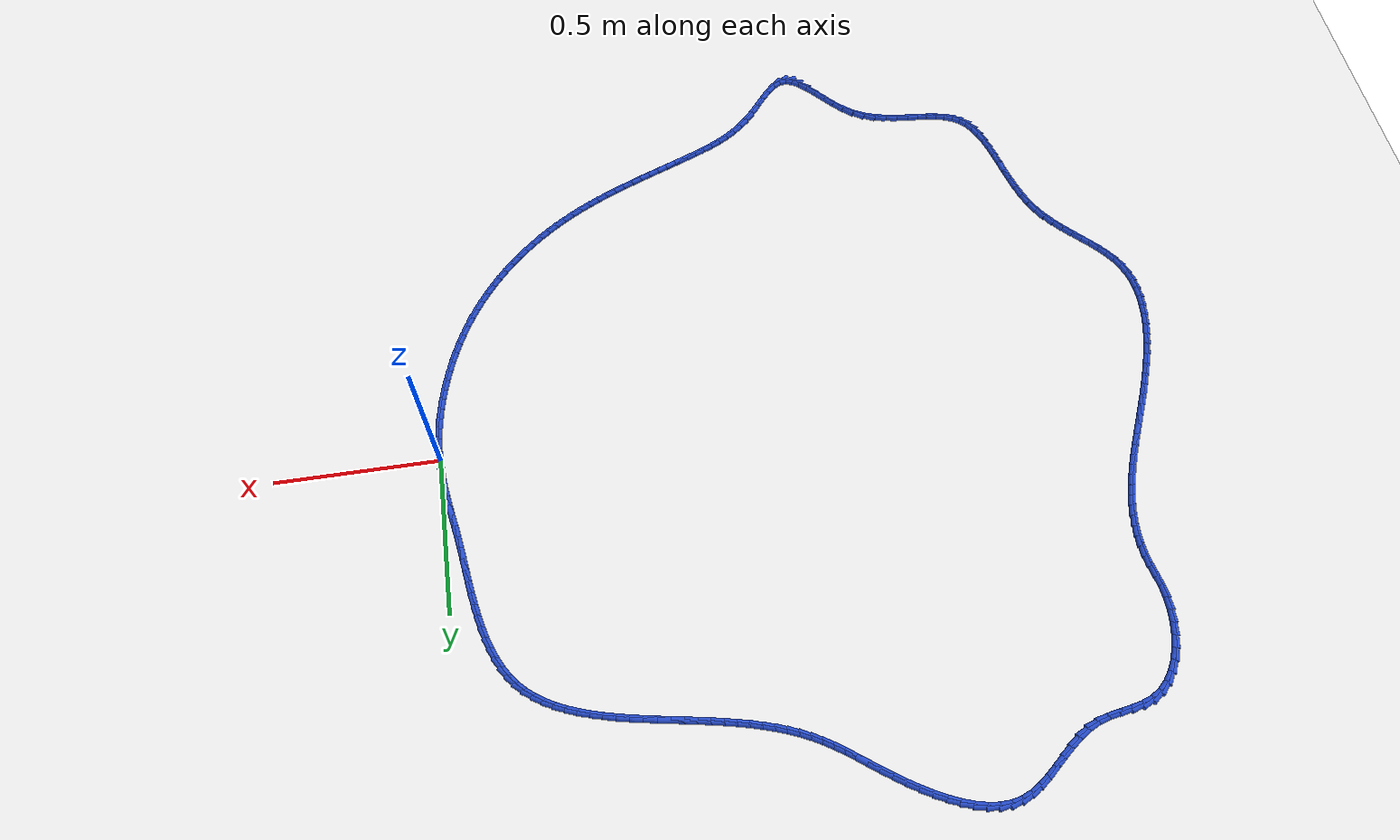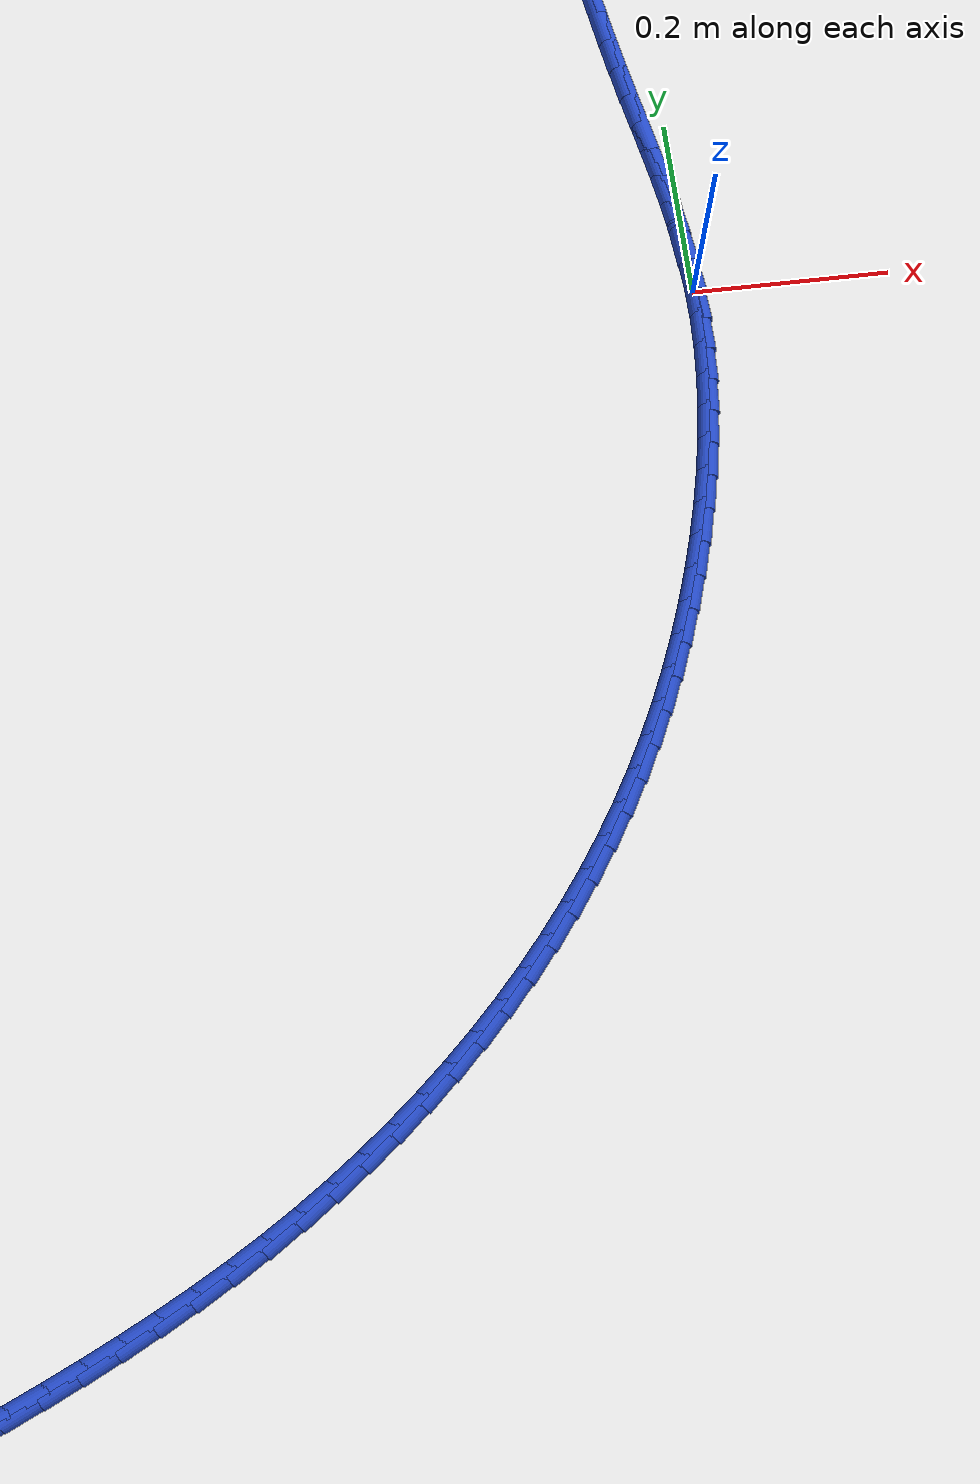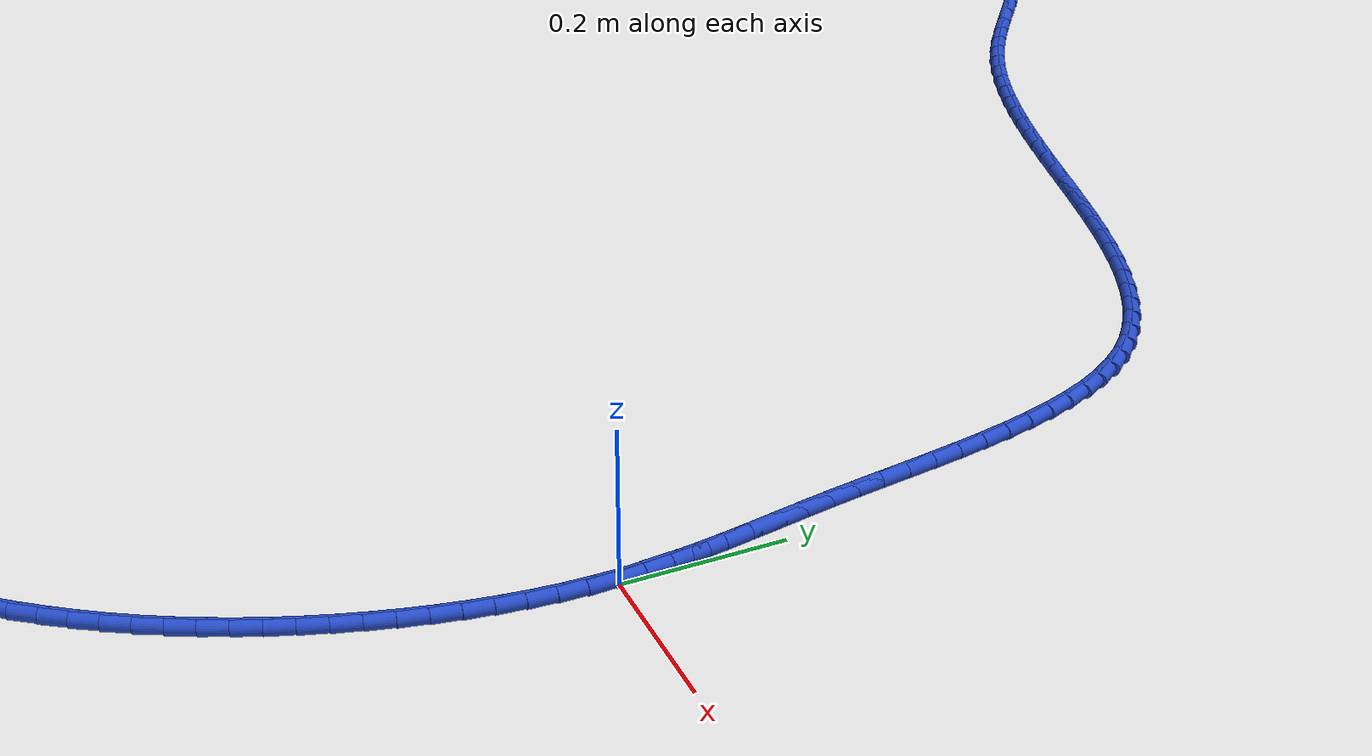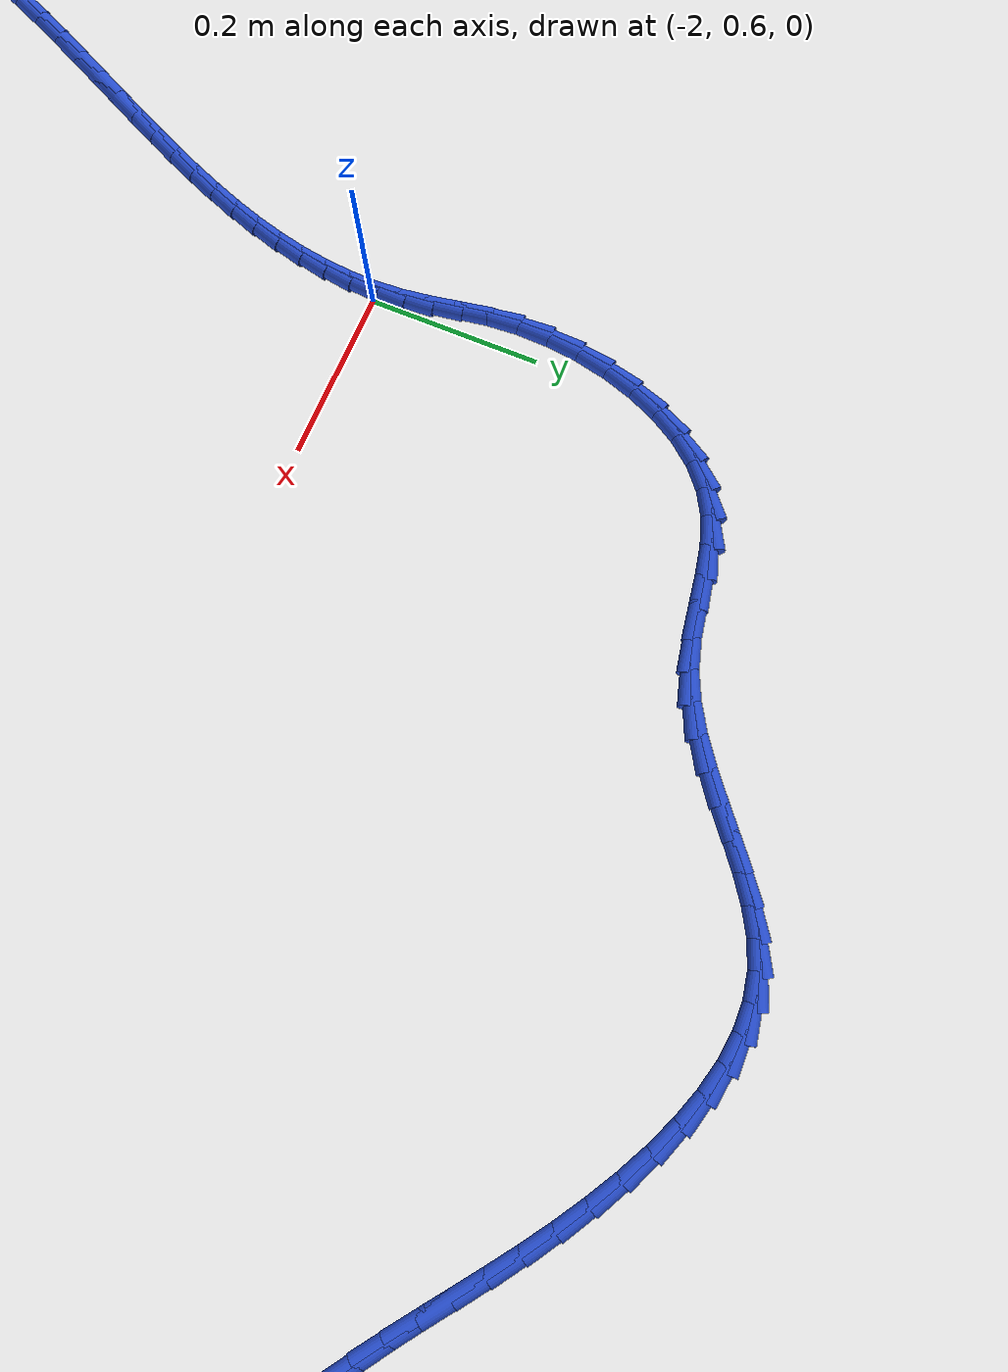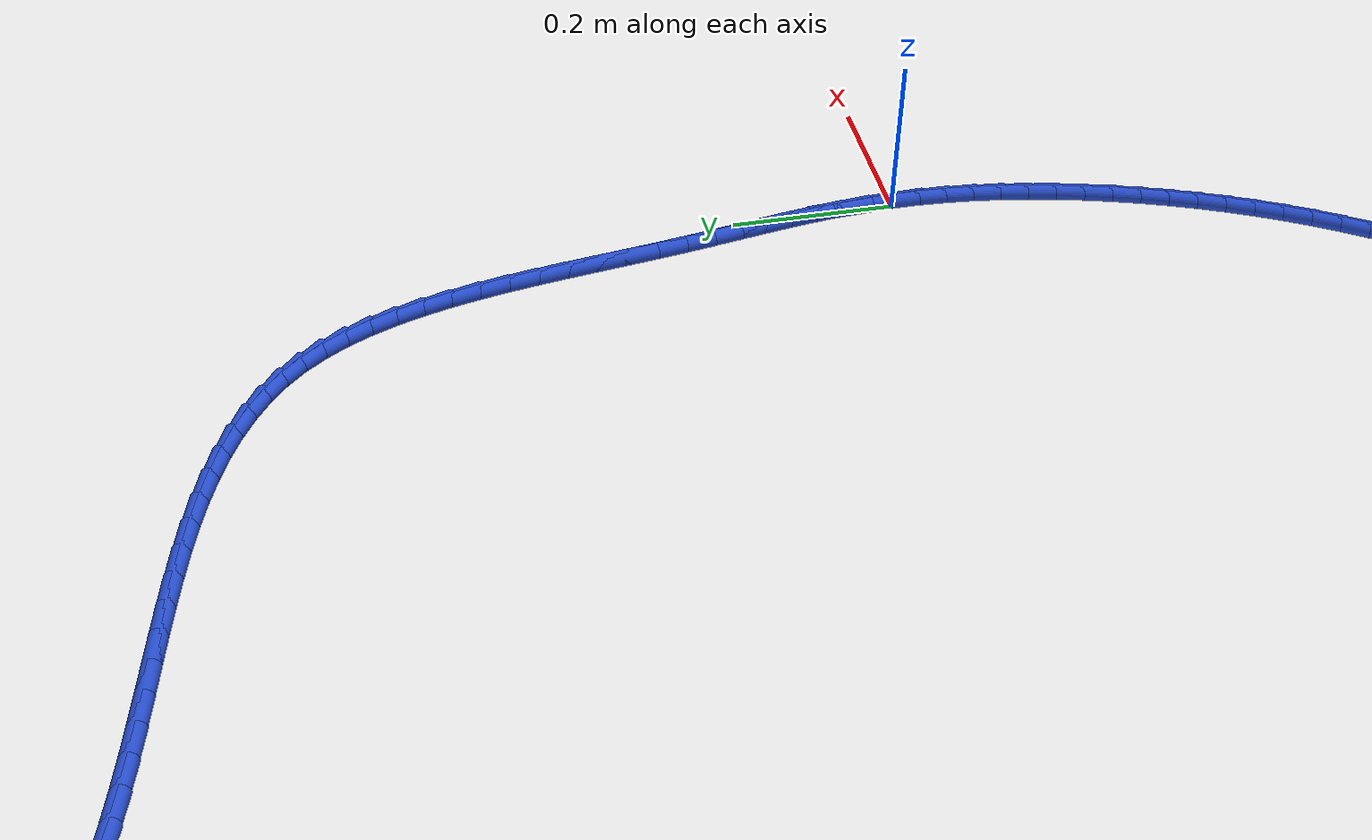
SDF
<sdf version="1.6">
 <world name="default">
  <light name="sun" type="directional">
   <pose>0 0 10 0 -0 0</pose>
   <diffuse>0.8 0.8 0.8 1</diffuse>
   <specular>0.2 0.2 0.2 1</specular>
   <attenuation>
    <range>1000</range>
    <constant>0.9</constant>
    <linear>0.01</linear>
    <quadratic>0.001</quadratic>
   </attenuation>
   <direction>-0.5 0.1 -0.9</direction>
  </light>
  <model name="ground_plane">
   <static>1</static>
   <link name="link">
    <collision name="collision">
     <geometry><plane><normal>0 0 1</normal><size>100 100</size></plane></geometry>
     <surface><friction><ode><mu>100</mu><mu2>50</mu2></ode></friction></surface>
    </collision>
    <visual name="visual">
     <cast_shadows>0</cast_shadows>
     <geometry><plane><normal>0 0 1</normal><size>100 100</size></plane></geometry>
     <material>
      <script><uri>file://media/materials/scripts/gazebo.material</uri><name>Gazebo/WhiteGlow</name></script>
     </material>
    </visual>
   </link>
  </model>
  <gravity>0 0 -9.8</gravity>
  <magnetic_field>6e-06 2.3e-05 -4.2e-05</magnetic_field>
  <atmosphere type="adiabatic"/>
  <physics name="default_physics" default="0" type="ode">
   <max_step_size>0.001</max_step_size>
   <real_time_factor>1</real_time_factor>
   <real_time_update_rate>1000</real_time_update_rate>
  </physics>
  <scene><ambient>0.4 0.4 0.4 1</ambient><background>0.7 0.7 0.7 1</background><shadows>1</shadows></scene>
  <spherical_coordinates>
   <surface_model>EARTH_WGS84</surface_model>
   <latitude_deg>0</latitude_deg>
   <longitude_deg>0</longitude_deg>
   <elevation>0</elevation>
   <heading_deg>0</heading_deg>
  </spherical_coordinates>
  <model name="line">
   <link name="link_0">
    <pose>-1.0408340855860843e-17 1.3877787807814457e-17 0.01 0 1.57 -1.5174585784094434</pose>
    <collision name="collision">
     <geometry><cylinder><radius>0.01</radius><length>0.08</length></cylinder></geometry>
    </collision>
    <visual name="visual">
     <material>
      <script><name>Gazebo/Blue</name><uri>file://media/materials/scripts/gazebo.material</uri></script>
     </material>
     <geometry><cylinder><radius>0.01</radius><length>0.08</length></cylinder></geometry>
    </visual>
   </link>
   <link name="link_1">
    <pose>-0.001797787003894169 0.03367374672130932 0.01 0 1.57 -1.4763028641299707</pose>
    <collision name="collision">
     <geometry><cylinder><radius>0.01</radius><length>0.08</length></cylinder></geometry>
    </collision>
    <visual name="visual">
     <material>
      <script><name>Gazebo/Blue</name><uri>file://media/materials/scripts/gazebo.material</uri></script>
     </material>
     <geometry><cylinder><radius>0.01</radius><length>0.08</length></cylinder></geometry>
    </visual>
   </link>
   <link name="link_2">
    <pose>-0.004974677567229655 0.06719383731850173 0.01 0 1.57 -1.4429940075132388</pose>
    <collision name="collision">
     <geometry><cylinder><radius>0.01</radius><length>0.08</length></cylinder></geometry>
    </collision>
    <visual name="visual">
     <material>
      <script><name>Gazebo/Blue</name><uri>file://media/materials/scripts/gazebo.material</uri></script>
     </material>
     <geometry><cylinder><radius>0.01</radius><length>0.08</length></cylinder></geometry>
    </visual>
   </link>
   <link name="link_3">
    <pose>-0.009276868182909811 0.10067321323386505 0.01 0 1.57 -1.4178004778522653</pose>
    <collision name="collision">
     <geometry><cylinder><radius>0.01</radius><length>0.08</length></cylinder></geometry>
    </collision>
    <visual name="visual">
     <material>
      <script><name>Gazebo/Blue</name><uri>file://media/materials/scripts/gazebo.material</uri></script>
     </material>
     <geometry><cylinder><radius>0.01</radius><length>0.08</length></cylinder></geometry>
    </visual>
   </link>
   <link name="link_4">
    <pose>-0.014450555343837983 0.13422481590968718 0.01 0 1.57 -1.4007896088642688</pose>
    <collision name="collision">
     <geometry><cylinder><radius>0.01</radius><length>0.08</length></cylinder></geometry>
    </collision>
    <visual name="visual">
     <material>
      <script><name>Gazebo/Blue</name><uri>file://media/materials/scripts/gazebo.material</uri></script>
     </material>
     <geometry><cylinder><radius>0.01</radius><length>0.08</length></cylinder></geometry>
    </visual>
   </link>
   <link name="link_5">
    <pose>-0.020241935542917505 0.16796158678825582 0.01 0 1.57 -1.3918784342253012</pose>
    <collision name="collision">
     <geometry><cylinder><radius>0.01</radius><length>0.08</length></cylinder></geometry>
    </collision>
    <visual name="visual">
     <material>
      <script><name>Gazebo/Blue</name><uri>file://media/materials/scripts/gazebo.material</uri></script>
     </material>
     <geometry><cylinder><radius>0.01</radius><length>0.08</length></cylinder></geometry>
    </visual>
   </link>
   <link name="link_6">
    <pose>-0.026397205273051724 0.20199646731185883 0.01 0 1.57 -1.3908737222804748</pose>
    <collision name="collision">
     <geometry><cylinder><radius>0.01</radius><length>0.08</length></cylinder></geometry>
    </collision>
    <visual name="visual">
     <material>
      <script><name>Gazebo/Blue</name><uri>file://media/materials/scripts/gazebo.material</uri></script>
     </material>
     <geometry><cylinder><radius>0.01</radius><length>0.08</length></cylinder></geometry>
    </visual>
   </link>
   <link name="link_7">
    <pose>-0.03266256102714396 0.23644239892278401 0.01 0 1.57 -1.3974979000075152</pose>
    <collision name="collision">
     <geometry><cylinder><radius>0.01</radius><length>0.08</length></cylinder></geometry>
    </collision>
    <visual name="visual">
     <material>
      <script><name>Gazebo/Blue</name><uri>file://media/materials/scripts/gazebo.material</uri></script>
     </material>
     <geometry><cylinder><radius>0.01</radius><length>0.08</length></cylinder></geometry>
    </visual>
   </link>
   <link name="link_8">
    <pose>-0.03878419929809761 0.2714123230633193 0.01 0 1.57 -1.410540140383066</pose>
    <collision name="collision">
     <geometry><cylinder><radius>0.01</radius><length>0.08</length></cylinder></geometry>
    </collision>
    <visual name="visual">
     <material>
      <script><name>Gazebo/Blue</name><uri>file://media/materials/scripts/gazebo.material</uri></script>
     </material>
     <geometry><cylinder><radius>0.01</radius><length>0.08</length></cylinder></geometry>
    </visual>
   </link>
   <link name="link_9">
    <pose>-0.044536545742731845 0.30699920457989194 0.01 0 1.57 -1.4211945639011299</pose>
    <collision name="collision">
     <geometry><cylinder><radius>0.01</radius><length>0.08</length></cylinder></geometry>
    </collision>
    <visual name="visual">
     <material>
      <script><name>Gazebo/Blue</name><uri>file://media/materials/scripts/gazebo.material</uri></script>
     </material>
     <geometry><cylinder><radius>0.01</radius><length>0.08</length></cylinder></geometry>
    </visual>
   </link>
   <link name="link_10">
    <pose>-0.049977274686973584 0.34309556511035183 0.01 0 1.57 -1.4247883033095197</pose>
    <collision name="collision">
     <geometry><cylinder><radius>0.01</radius><length>0.08</length></cylinder></geometry>
    </collision>
    <visual name="visual">
     <material>
      <script><name>Gazebo/Blue</name><uri>file://media/materials/scripts/gazebo.material</uri></script>
     </material>
     <geometry><cylinder><radius>0.01</radius><length>0.08</length></cylinder></geometry>
    </visual>
   </link>
   <link name="link_11">
    <pose>-0.05532751325703738 0.3794782575981681 0.01 0 1.57 -1.421472245109235</pose>
    <collision name="collision">
     <geometry><cylinder><radius>0.01</radius><length>0.08</length></cylinder></geometry>
    </collision>
    <visual name="visual">
     <material>
      <script><name>Gazebo/Blue</name><uri>file://media/materials/scripts/gazebo.material</uri></script>
     </material>
     <geometry><cylinder><radius>0.01</radius><length>0.08</length></cylinder></geometry>
    </visual>
   </link>
   <link name="link_12">
    <pose>-0.06081036401106876 0.4159227370564483 0.01 0 1.57 -1.4112411787081625</pose>
    <collision name="collision">
     <geometry><cylinder><radius>0.01</radius><length>0.08</length></cylinder></geometry>
    </collision>
    <visual name="visual">
     <material>
      <script><name>Gazebo/Blue</name><uri>file://media/materials/scripts/gazebo.material</uri></script>
     </material>
     <geometry><cylinder><radius>0.01</radius><length>0.08</length></cylinder></geometry>
    </visual>
   </link>
   <link name="link_13">
    <pose>-0.06664892950721323 0.4522044584982996 0.01 0 1.57 -1.3938805285159337</pose>
    <collision name="collision">
     <geometry><cylinder><radius>0.01</radius><length>0.08</length></cylinder></geometry>
    </collision>
    <visual name="visual">
     <material>
      <script><name>Gazebo/Blue</name><uri>file://media/materials/scripts/gazebo.material</uri></script>
     </material>
     <geometry><cylinder><radius>0.01</radius><length>0.08</length></cylinder></geometry>
    </visual>
   </link>
   <link name="link_14">
    <pose>-0.07306631230361622 0.48809887693682935 0.01 0 1.57 -1.36896833246314</pose>
    <collision name="collision">
     <geometry><cylinder><radius>0.01</radius><length>0.08</length></cylinder></geometry>
    </collision>
    <visual name="visual">
     <material>
      <script><name>Gazebo/Blue</name><uri>file://media/materials/scripts/gazebo.material</uri></script>
     </material>
     <geometry><cylinder><radius>0.01</radius><length>0.08</length></cylinder></geometry>
    </visual>
   </link>
   <link name="link_15">
    <pose>-0.08028561495842329 0.5233814473851446 0.01 0 1.57 -1.3358761266931571</pose>
    <collision name="collision">
     <geometry><cylinder><radius>0.01</radius><length>0.08</length></cylinder></geometry>
    </collision>
    <visual name="visual">
     <material>
      <script><name>Gazebo/Blue</name><uri>file://media/materials/scripts/gazebo.material</uri></script>
     </material>
     <geometry><cylinder><radius>0.01</radius><length>0.08</length></cylinder></geometry>
    </visual>
   </link>
   <link name="link_16">
    <pose>-0.08852994002977994 0.5578276248563532 0.01 0 1.57 -1.29377625659038</pose>
    <collision name="collision">
     <geometry><cylinder><radius>0.01</radius><length>0.08</length></cylinder></geometry>
    </collision>
    <visual name="visual">
     <material>
      <script><name>Gazebo/Blue</name><uri>file://media/materials/scripts/gazebo.material</uri></script>
     </material>
     <geometry><cylinder><radius>0.01</radius><length>0.08</length></cylinder></geometry>
    </visual>
   </link>
   <link name="link_17">
    <pose>-0.09802239007583166 0.591212864363562 0.01 0 1.57 -1.2416689302785737</pose>
    <collision name="collision">
     <geometry><cylinder><radius>0.01</radius><length>0.08</length></cylinder></geometry>
    </collision>
    <visual name="visual">
     <material>
      <script><name>Gazebo/Blue</name><uri>file://media/materials/scripts/gazebo.material</uri></script>
     </material>
     <geometry><cylinder><radius>0.01</radius><length>0.08</length></cylinder></geometry>
    </visual>
   </link>
   <link name="link_18">
    <pose>-0.1089860676547239 0.6233126209198782 0.01 0 1.57 -1.1784509092266642</pose>
    <collision name="collision">
     <geometry><cylinder><radius>0.01</radius><length>0.08</length></cylinder></geometry>
    </collision>
    <visual name="visual">
     <material>
      <script><name>Gazebo/Blue</name><uri>file://media/materials/scripts/gazebo.material</uri></script>
     </material>
     <geometry><cylinder><radius>0.01</radius><length>0.08</length></cylinder></geometry>
    </visual>
   </link>
   <link name="link_19">
    <pose>-0.1216440753246022 0.6539023495384093 0.01 0 1.57 -1.1030576861954953</pose>
    <collision name="collision">
     <geometry><cylinder><radius>0.01</radius><length>0.08</length></cylinder></geometry>
    </collision>
    <visual name="visual">
     <material>
      <script><name>Gazebo/Blue</name><uri>file://media/materials/scripts/gazebo.material</uri></script>
     </material>
     <geometry><cylinder><radius>0.01</radius><length>0.08</length></cylinder></geometry>
    </visual>
   </link>
   <link name="link_20">
    <pose>-0.13621951564361212 0.6827575052322629 0.01 0 1.57 -1.0147154639845146</pose>
    <collision name="collision">
     <geometry><cylinder><radius>0.01</radius><length>0.08</length></cylinder></geometry>
    </collision>
    <visual name="visual">
     <material>
      <script><name>Gazebo/Blue</name><uri>file://media/materials/scripts/gazebo.material</uri></script>
     </material>
     <geometry><cylinder><radius>0.01</radius><length>0.08</length></cylinder></geometry>
    </visual>
   </link>
   <link name="link_21">
    <pose>-0.152935491169899 0.7096535430145458 0.01 0 1.57 -0.9133211662812847</pose>
    <collision name="collision">
     <geometry><cylinder><radius>0.01</radius><length>0.08</length></cylinder></geometry>
    </collision>
    <visual name="visual">
     <material>
      <script><name>Gazebo/Blue</name><uri>file://media/materials/scripts/gazebo.material</uri></script>
     </material>
     <geometry><cylinder><radius>0.01</radius><length>0.08</length></cylinder></geometry>
    </visual>
   </link>
   <link name="link_22">
    <pose>-0.17201510446160845 0.7343659178983653 0.01 0 1.57 -0.802004961885333</pose>
    <collision name="collision">
     <geometry><cylinder><radius>0.01</radius><length>0.08</length></cylinder></geometry>
    </collision>
    <visual name="visual">
     <material>
      <script><name>Gazebo/Blue</name><uri>file://media/materials/scripts/gazebo.material</uri></script>
     </material>
     <geometry><cylinder><radius>0.01</radius><length>0.08</length></cylinder></geometry>
    </visual>
   </link>
   <link name="link_23">
    <pose>-0.1936335747154588 0.7567146090715287 0.01 0 1.57 -0.6954426829183508</pose>
    <collision name="collision">
     <geometry><cylinder><radius>0.01</radius><length>0.08</length></cylinder></geometry>
    </collision>
    <visual name="visual">
     <material>
      <script><name>Gazebo/Blue</name><uri>file://media/materials/scripts/gazebo.material</uri></script>
     </material>
     <geometry><cylinder><radius>0.01</radius><length>0.08</length></cylinder></geometry>
    </visual>
   </link>
   <link name="link_24">
    <pose>-0.21768205709597643 0.776783731660052 0.01 0 1.57 -0.6000425534046825</pose>
    <collision name="collision">
     <geometry><cylinder><radius>0.01</radius><length>0.08</length></cylinder></geometry>
    </collision>
    <visual name="visual">
     <material>
      <script><name>Gazebo/Blue</name><uri>file://media/materials/scripts/gazebo.material</uri></script>
     </material>
     <geometry><cylinder><radius>0.01</radius><length>0.08</length></cylinder></geometry>
    </visual>
   </link>
   <link name="link_25">
    <pose>-0.24394735644211527 0.7947544305720565 0.01 0 1.57 -0.5164751111016785</pose>
    <collision name="collision">
     <geometry><cylinder><radius>0.01</radius><length>0.08</length></cylinder></geometry>
    </collision>
    <visual name="visual">
     <material>
      <script><name>Gazebo/Blue</name><uri>file://media/materials/scripts/gazebo.material</uri></script>
     </material>
     <geometry><cylinder><radius>0.01</radius><length>0.08</length></cylinder></geometry>
    </visual>
   </link>
   <link name="link_26">
    <pose>-0.2722161173716004 0.810807999696808 0.01 0 1.57 -0.4445273258515845</pose>
    <collision name="collision">
     <geometry><cylinder><radius>0.01</radius><length>0.08</length></cylinder></geometry>
    </collision>
    <visual name="visual">
     <material>
      <script><name>Gazebo/Blue</name><uri>file://media/materials/scripts/gazebo.material</uri></script>
     </material>
     <geometry><cylinder><radius>0.01</radius><length>0.08</length></cylinder></geometry>
    </visual>
   </link>
   <link name="link_27">
    <pose>-0.302274984502157 0.8251257329235725 0.01 0 1.57 -0.38347156673775146</pose>
    <collision name="collision">
     <geometry><cylinder><radius>0.01</radius><length>0.08</length></cylinder></geometry>
    </collision>
    <visual name="visual">
     <material>
      <script><name>Gazebo/Blue</name><uri>file://media/materials/scripts/gazebo.material</uri></script>
     </material>
     <geometry><cylinder><radius>0.01</radius><length>0.08</length></cylinder></geometry>
    </visual>
   </link>
   <link name="link_28">
    <pose>-0.33391060245151 0.837888924141616 0.01 0 1.57 -0.33235662382471465</pose>
    <collision name="collision">
     <geometry><cylinder><radius>0.01</radius><length>0.08</length></cylinder></geometry>
    </collision>
    <visual name="visual">
     <material>
      <script><name>Gazebo/Blue</name><uri>file://media/materials/scripts/gazebo.material</uri></script>
     </material>
     <geometry><cylinder><radius>0.01</radius><length>0.08</length></cylinder></geometry>
    </visual>
   </link>
   <link name="link_29">
    <pose>-0.3669096158373849 0.8492788672402043 0.01 0 1.57 -0.29020097385252064</pose>
    <collision name="collision">
     <geometry><cylinder><radius>0.01</radius><length>0.08</length></cylinder></geometry>
    </collision>
    <visual name="visual">
     <material>
      <script><name>Gazebo/Blue</name><uri>file://media/materials/scripts/gazebo.material</uri></script>
     </material>
     <geometry><cylinder><radius>0.01</radius><length>0.08</length></cylinder></geometry>
    </visual>
   </link>
   <link name="link_30">
    <pose>-0.40105866927750633 0.8594768561086029 0.01 0 1.57 -0.25610354938143925</pose>
    <collision name="collision">
     <geometry><cylinder><radius>0.01</radius><length>0.08</length></cylinder></geometry>
    </collision>
    <visual name="visual">
     <material>
      <script><name>Gazebo/Blue</name><uri>file://media/materials/scripts/gazebo.material</uri></script>
     </material>
     <geometry><cylinder><radius>0.01</radius><length>0.08</length></cylinder></geometry>
    </visual>
   </link>
   <link name="link_31">
    <pose>-0.4361444073895997 0.8686641846360783 0.01 0 1.57 -0.2292984868983398</pose>
    <collision name="collision">
     <geometry><cylinder><radius>0.01</radius><length>0.08</length></cylinder></geometry>
    </collision>
    <visual name="visual">
     <material>
      <script><name>Gazebo/Blue</name><uri>file://media/materials/scripts/gazebo.material</uri></script>
     </material>
     <geometry><cylinder><radius>0.01</radius><length>0.08</length></cylinder></geometry>
    </visual>
   </link>
   <link name="link_32">
    <pose>-0.47195347479138994 0.8770221467118957 0.01 0 1.57 -0.2091770866374355</pose>
    <collision name="collision">
     <geometry><cylinder><radius>0.01</radius><length>0.08</length></cylinder></geometry>
    </collision>
    <visual name="visual">
     <material>
      <script><name>Gazebo/Blue</name><uri>file://media/materials/scripts/gazebo.material</uri></script>
     </material>
     <geometry><cylinder><radius>0.01</radius><length>0.08</length></cylinder></geometry>
    </visual>
   </link>
   <link name="link_33">
    <pose>-0.5082725161006023 0.8847320362253212 0.01 0 1.57 -0.19529330008092677</pose>
    <collision name="collision">
     <geometry><cylinder><radius>0.01</radius><length>0.08</length></cylinder></geometry>
    </collision>
    <visual name="visual">
     <material>
      <script><name>Gazebo/Blue</name><uri>file://media/materials/scripts/gazebo.material</uri></script>
     </material>
     <geometry><cylinder><radius>0.01</radius><length>0.08</length></cylinder></geometry>
    </visual>
   </link>
   <link name="link_34">
    <pose>-0.5448881759349619 0.8919751470656209 0.01 0 1.57 -0.18736297332701268</pose>
    <collision name="collision">
     <geometry><cylinder><radius>0.01</radius><length>0.08</length></cylinder></geometry>
    </collision>
    <visual name="visual">
     <material>
      <script><name>Gazebo/Blue</name><uri>file://media/materials/scripts/gazebo.material</uri></script>
     </material>
     <geometry><cylinder><radius>0.01</radius><length>0.08</length></cylinder></geometry>
    </visual>
   </link>
   <link name="link_35">
    <pose>-0.5815870989121935 0.8989327731220603 0.01 0 1.57 -0.18526287010277862</pose>
    <collision name="collision">
     <geometry><cylinder><radius>0.01</radius><length>0.08</length></cylinder></geometry>
    </collision>
    <visual name="visual">
     <material>
      <script><name>Gazebo/Blue</name><uri>file://media/materials/scripts/gazebo.material</uri></script>
     </material>
     <geometry><cylinder><radius>0.01</radius><length>0.08</length></cylinder></geometry>
    </visual>
   </link>
   <link name="link_36">
    <pose>-0.6181559296500225 0.9057862082839054 0.01 0 1.57 -0.1890318658535839</pose>
    <collision name="collision">
     <geometry><cylinder><radius>0.01</radius><length>0.08</length></cylinder></geometry>
    </collision>
    <visual name="visual">
     <material>
      <script><name>Gazebo/Blue</name><uri>file://media/materials/scripts/gazebo.material</uri></script>
     </material>
     <geometry><cylinder><radius>0.01</radius><length>0.08</length></cylinder></geometry>
    </visual>
   </link>
   <link name="link_37">
    <pose>-0.6543814149427474 0.9127167261872828 0.01 0 1.57 -0.1984312550376469</pose>
    <collision name="collision">
     <geometry><cylinder><radius>0.01</radius><length>0.08</length></cylinder></geometry>
    </collision>
    <visual name="visual">
     <material>
      <script><name>Gazebo/Blue</name><uri>file://media/materials/scripts/gazebo.material</uri></script>
     </material>
     <geometry><cylinder><radius>0.01</radius><length>0.08</length></cylinder></geometry>
    </visual>
   </link>
   <link name="link_38">
    <pose>-0.6900920482280765 0.919897325571596 0.01 0 1.57 -0.21258586765694568</pose>
    <collision name="collision">
     <geometry><cylinder><radius>0.01</radius><length>0.08</length></cylinder></geometry>
    </collision>
    <visual name="visual">
     <material>
      <script><name>Gazebo/Blue</name><uri>file://media/materials/scripts/gazebo.material</uri></script>
     </material>
     <geometry><cylinder><radius>0.01</radius><length>0.08</length></cylinder></geometry>
    </visual>
   </link>
   <link name="link_39">
    <pose>-0.7252220674548802 0.9274800448106381 0.01 0 1.57 -0.2315281517118318</pose>
    <collision name="collision">
     <geometry><cylinder><radius>0.01</radius><length>0.08</length></cylinder></geometry>
    </collision>
    <visual name="visual">
     <material>
      <script><name>Gazebo/Blue</name><uri>file://media/materials/scripts/gazebo.material</uri></script>
     </material>
     <geometry><cylinder><radius>0.01</radius><length>0.08</length></cylinder></geometry>
    </visual>
   </link>
   <link name="link_40">
    <pose>-0.7597222004778517 0.9356136536976304 0.01 0 1.57 -0.2554704260942258</pose>
    <collision name="collision">
     <geometry><cylinder><radius>0.01</radius><length>0.08</length></cylinder></geometry>
    </collision>
    <visual name="visual">
     <material>
      <script><name>Gazebo/Blue</name><uri>file://media/materials/scripts/gazebo.material</uri></script>
     </material>
     <geometry><cylinder><radius>0.01</radius><length>0.08</length></cylinder></geometry>
    </visual>
   </link>
   <link name="link_41">
    <pose>-0.7935431751516822 0.9444469220257925 0.01 0 1.57 -0.28462118336087255</pose>
    <collision name="collision">
     <geometry><cylinder><radius>0.01</radius><length>0.08</length></cylinder></geometry>
    </collision>
    <visual name="visual">
     <material>
      <script><name>Gazebo/Blue</name><uri>file://media/materials/scripts/gazebo.material</uri></script>
     </material>
     <geometry><cylinder><radius>0.01</radius><length>0.08</length></cylinder></geometry>
    </visual>
   </link>
   <link name="link_42">
    <pose>-0.8266357193310648 0.9541286195883455 0.01 0 1.57 -0.31916606909875794</pose>
    <collision name="collision">
     <geometry><cylinder><radius>0.01</radius><length>0.08</length></cylinder></geometry>
    </collision>
    <visual name="visual">
     <material>
      <script><name>Gazebo/Blue</name><uri>file://media/materials/scripts/gazebo.material</uri></script>
     </material>
     <geometry><cylinder><radius>0.01</radius><length>0.08</length></cylinder></geometry>
    </visual>
   </link>
   <link name="link_43">
    <pose>-0.858950560870692 0.9648075161785099 0.01 0 1.57 -0.35924155960610293</pose>
    <collision name="collision">
     <geometry><cylinder><radius>0.01</radius><length>0.08</length></cylinder></geometry>
    </collision>
    <visual name="visual">
     <material>
      <script><name>Gazebo/Blue</name><uri>file://media/materials/scripts/gazebo.material</uri></script>
     </material>
     <geometry><cylinder><radius>0.01</radius><length>0.08</length></cylinder></geometry>
    </visual>
   </link>
   <link name="link_44">
    <pose>-0.8904384276252557 0.9766323815895059 0.01 0 1.57 -0.40490112511709003</pose>
    <collision name="collision">
     <geometry><cylinder><radius>0.01</radius><length>0.08</length></cylinder></geometry>
    </collision>
    <visual name="visual">
     <material>
      <script><name>Gazebo/Blue</name><uri>file://media/materials/scripts/gazebo.material</uri></script>
     </material>
     <geometry><cylinder><radius>0.01</radius><length>0.08</length></cylinder></geometry>
    </visual>
   </link>
   <link name="link_45">
    <pose>-0.9210500474494485 0.9897519856145541 0.01 0 1.57 -0.45607524401241484</pose>
    <collision name="collision">
     <geometry><cylinder><radius>0.01</radius><length>0.08</length></cylinder></geometry>
    </collision>
    <visual name="visual">
     <material>
      <script><name>Gazebo/Blue</name><uri>file://media/materials/scripts/gazebo.material</uri></script>
     </material>
     <geometry><cylinder><radius>0.01</radius><length>0.08</length></cylinder></geometry>
    </visual>
   </link>
   <link name="link_46">
    <pose>-0.9507361481979625 1.004315098046875 0.01 0 1.57 -0.5124961812330554</pose>
    <collision name="collision">
     <geometry><cylinder><radius>0.01</radius><length>0.08</length></cylinder></geometry>
    </collision>
    <visual name="visual">
     <material>
      <script><name>Gazebo/Blue</name><uri>file://media/materials/scripts/gazebo.material</uri></script>
     </material>
     <geometry><cylinder><radius>0.01</radius><length>0.08</length></cylinder></geometry>
    </visual>
   </link>
   <link name="link_47">
    <pose>-0.9794482579053531 1.0204696937088857 0.01 0 1.57 -0.5682101029825806</pose>
    <collision name="collision">
     <geometry><cylinder><radius>0.01</radius><length>0.08</length></cylinder></geometry>
    </collision>
    <visual name="visual">
     <material>
      <script><name>Gazebo/Blue</name><uri>file://media/materials/scripts/gazebo.material</uri></script>
     </material>
     <geometry><cylinder><radius>0.01</radius><length>0.08</length></cylinder></geometry>
    </visual>
   </link>
   <link name="link_48">
    <pose>-1.007270081614434 1.0382324308688509 0.01 0 1.57 -0.6108612249323891</pose>
    <collision name="collision">
     <geometry><cylinder><radius>0.01</radius><length>0.08</length></cylinder></geometry>
    </collision>
    <visual name="visual">
     <material>
      <script><name>Gazebo/Blue</name><uri>file://media/materials/scripts/gazebo.material</uri></script>
     </material>
     <geometry><cylinder><radius>0.01</radius><length>0.08</length></cylinder></geometry>
    </visual>
   </link>
   <link name="link_49">
    <pose>-1.034563664210379 1.0573434399066775 0.01 0 1.57 -0.6385932322571234</pose>
    <collision name="collision">
     <geometry><cylinder><radius>0.01</radius><length>0.08</length></cylinder></geometry>
    </collision>
    <visual name="visual">
     <material>
      <script><name>Gazebo/Blue</name><uri>file://media/materials/scripts/gazebo.material</uri></script>
     </material>
     <geometry><cylinder><radius>0.01</radius><length>0.08</length></cylinder></geometry>
    </visual>
   </link>
   <link name="link_50">
    <pose>-1.0617262714661142 1.0775078595976428 0.01 0 1.57 -0.6516476514790169</pose>
    <collision name="collision">
     <geometry><cylinder><radius>0.01</radius><length>0.08</length></cylinder></geometry>
    </collision>
    <visual name="visual">
     <material>
      <script><name>Gazebo/Blue</name><uri>file://media/materials/scripts/gazebo.material</uri></script>
     </material>
     <geometry><cylinder><radius>0.01</radius><length>0.08</length></cylinder></geometry>
    </visual>
   </link>
   <link name="link_51">
    <pose>-1.089155169154567 1.0984308287170261 0.01 0 1.57 -0.6506910893379694</pose>
    <collision name="collision">
     <geometry><cylinder><radius>0.01</radius><length>0.08</length></cylinder></geometry>
    </collision>
    <visual name="visual">
     <material>
      <script><name>Gazebo/Blue</name><uri>file://media/materials/scripts/gazebo.material</uri></script>
     </material>
     <geometry><cylinder><radius>0.01</radius><length>0.08</length></cylinder></geometry>
    </visual>
   </link>
   <link name="link_52">
    <pose>-1.1172476230486637 1.119817486040106 0.01 0 1.57 -0.6366725882809615</pose>
    <collision name="collision">
     <geometry><cylinder><radius>0.01</radius><length>0.08</length></cylinder></geometry>
    </collision>
    <visual name="visual">
     <material>
      <script><name>Gazebo/Blue</name><uri>file://media/materials/scripts/gazebo.material</uri></script>
     </material>
     <geometry><cylinder><radius>0.01</radius><length>0.08</length></cylinder></geometry>
    </visual>
   </link>
   <link name="link_53">
    <pose>-1.1464008989213303 1.14137297034216 0.01 0 1.57 -0.6113380053937765</pose>
    <collision name="collision">
     <geometry><cylinder><radius>0.01</radius><length>0.08</length></cylinder></geometry>
    </collision>
    <visual name="visual">
     <material>
      <script><name>Gazebo/Blue</name><uri>file://media/materials/scripts/gazebo.material</uri></script>
     </material>
     <geometry><cylinder><radius>0.01</radius><length>0.08</length></cylinder></geometry>
    </visual>
   </link>
   <link name="link_54">
    <pose>-1.176917898651941 1.1627627117914263 0.01 0 1.57 -0.5780427387369828</pose>
    <collision name="collision">
     <geometry><cylinder><radius>0.01</radius><length>0.08</length></cylinder></geometry>
    </collision>
    <visual name="visual">
     <material>
      <script><name>Gazebo/Blue</name><uri>file://media/materials/scripts/gazebo.material</uri></script>
     </material>
     <geometry><cylinder><radius>0.01</radius><length>0.08</length></cylinder></geometry>
    </visual>
   </link>
   <link name="link_55">
    <pose>-1.2086422637118477 1.1834588824106278 0.01 0 1.57 -0.5366835123935262</pose>
    <collision name="collision">
     <geometry><cylinder><radius>0.01</radius><length>0.08</length></cylinder></geometry>
    </collision>
    <visual name="visual">
     <material>
      <script><name>Gazebo/Blue</name><uri>file://media/materials/scripts/gazebo.material</uri></script>
     </material>
     <geometry><cylinder><radius>0.01</radius><length>0.08</length></cylinder></geometry>
    </visual>
   </link>
   <link name="link_56">
    <pose>-1.241278121779455 1.2028749464035091 0.01 0 1.57 -0.4856228797664288</pose>
    <collision name="collision">
     <geometry><cylinder><radius>0.01</radius><length>0.08</length></cylinder></geometry>
    </collision>
    <visual name="visual">
     <material>
      <script><name>Gazebo/Blue</name><uri>file://media/materials/scripts/gazebo.material</uri></script>
     </material>
     <geometry><cylinder><radius>0.01</radius><length>0.08</length></cylinder></geometry>
    </visual>
   </link>
   <link name="link_57">
    <pose>-1.2745295684713251 1.2204243544820943 0.01 0 1.57 -0.4225862140601892</pose>
    <collision name="collision">
     <geometry><cylinder><radius>0.01</radius><length>0.08</length></cylinder></geometry>
    </collision>
    <visual name="visual">
     <material>
      <script><name>Gazebo/Blue</name><uri>file://media/materials/scripts/gazebo.material</uri></script>
     </material>
     <geometry><cylinder><radius>0.01</radius><length>0.08</length></cylinder></geometry>
    </visual>
   </link>
   <link name="link_58">
    <pose>-1.3081006994040179 1.235520557358408 0.01 0 1.57 -0.3445612678087705</pose>
    <collision name="collision">
     <geometry><cylinder><radius>0.01</radius><length>0.08</length></cylinder></geometry>
    </collision>
    <visual name="visual">
     <material>
      <script><name>Gazebo/Blue</name><uri>file://media/materials/scripts/gazebo.material</uri></script>
     </material>
     <geometry><cylinder><radius>0.01</radius><length>0.08</length></cylinder></geometry>
    </visual>
   </link>
   <link name="link_59">
    <pose>-1.3416956101940962 1.2475770057444757 0.01 0 1.57 -0.24778551821294031</pose>
    <collision name="collision">
     <geometry><cylinder><radius>0.01</radius><length>0.08</length></cylinder></geometry>
    </collision>
    <visual name="visual">
     <material>
      <script><name>Gazebo/Blue</name><uri>file://media/materials/scripts/gazebo.material</uri></script>
     </material>
     <geometry><cylinder><radius>0.01</radius><length>0.08</length></cylinder></geometry>
    </visual>
   </link>
   <link name="link_60">
    <pose>-1.3750183964581197 1.2560071503523214 0.01 0 1.57 -0.12804908183256347</pose>
    <collision name="collision">
     <geometry><cylinder><radius>0.01</radius><length>0.08</length></cylinder></geometry>
    </collision>
    <visual name="visual">
     <material>
      <script><name>Gazebo/Blue</name><uri>file://media/materials/scripts/gazebo.material</uri></script>
     </material>
     <geometry><cylinder><radius>0.01</radius><length>0.08</length></cylinder></geometry>
    </visual>
   </link>
   <link name="link_61">
    <pose>-1.407773153812651 1.26022444189397 0.01 0 1.57 0.01825121153832464</pose>
    <collision name="collision">
     <geometry><cylinder><radius>0.01</radius><length>0.08</length></cylinder></geometry>
    </collision>
    <visual name="visual">
     <material>
      <script><name>Gazebo/Blue</name><uri>file://media/materials/scripts/gazebo.material</uri></script>
     </material>
     <geometry><cylinder><radius>0.01</radius><length>0.08</length></cylinder></geometry>
    </visual>
   </link>
   <link name="link_62">
    <pose>-1.4396639778742502 1.2596423310814466 0.01 0 1.57 0.1918146178247075</pose>
    <collision name="collision">
     <geometry><cylinder><radius>0.01</radius><length>0.08</length></cylinder></geometry>
    </collision>
    <visual name="visual">
     <material>
      <script><name>Gazebo/Blue</name><uri>file://media/materials/scripts/gazebo.material</uri></script>
     </material>
     <geometry><cylinder><radius>0.01</radius><length>0.08</length></cylinder></geometry>
    </visual>
   </link>
   <link name="link_63">
    <pose>-1.4703949768707225 1.2536743025000623 0.01 0 1.57 0.3755300517845556</pose>
    <collision name="collision">
     <geometry><cylinder><radius>0.01</radius><length>0.08</length></cylinder></geometry>
    </collision>
    <visual name="visual">
     <material>
      <script><name>Gazebo/Blue</name><uri>file://media/materials/scripts/gazebo.material</uri></script>
     </material>
     <geometry><cylinder><radius>0.01</radius><length>0.08</length></cylinder></geometry>
    </visual>
   </link>
   <link name="link_64">
    <pose>-1.4997997984988494 1.242081778474179 0.01 0 1.57 0.5203321534626906</pose>
    <collision name="collision">
     <geometry><cylinder><radius>0.01</radius><length>0.08</length></cylinder></geometry>
    </collision>
    <visual name="visual">
     <material>
      <script><name>Gazebo/Blue</name><uri>file://media/materials/scripts/gazebo.material</uri></script>
     </material>
     <geometry><cylinder><radius>0.01</radius><length>0.08</length></cylinder></geometry>
    </visual>
   </link>
   <link name="link_65">
    <pose>-1.5281606293536816 1.2258309385451978 0.01 0 1.57 0.6178428762638112</pose>
    <collision name="collision">
     <geometry><cylinder><radius>0.01</radius><length>0.08</length></cylinder></geometry>
    </collision>
    <visual name="visual">
     <material>
      <script><name>Gazebo/Blue</name><uri>file://media/materials/scripts/gazebo.material</uri></script>
     </material>
     <geometry><cylinder><radius>0.01</radius><length>0.08</length></cylinder></geometry>
    </visual>
   </link>
   <link name="link_66">
    <pose>-1.5558566707289896 1.2061485397850091 0.01 0 1.57 0.6738246059617238</pose>
    <collision name="collision">
     <geometry><cylinder><radius>0.01</radius><length>0.08</length></cylinder></geometry>
    </collision>
    <visual name="visual">
     <material>
      <script><name>Gazebo/Blue</name><uri>file://media/materials/scripts/gazebo.material</uri></script>
     </material>
     <geometry><cylinder><radius>0.01</radius><length>0.08</length></cylinder></geometry>
    </visual>
   </link>
   <link name="link_67">
    <pose>-1.5832671239185419 1.1842613392655037 0.01 0 1.57 0.6935610456259537</pose>
    <collision name="collision">
     <geometry><cylinder><radius>0.01</radius><length>0.08</length></cylinder></geometry>
    </collision>
    <visual name="visual">
     <material>
      <script><name>Gazebo/Blue</name><uri>file://media/materials/scripts/gazebo.material</uri></script>
     </material>
     <geometry><cylinder><radius>0.01</radius><length>0.08</length></cylinder></geometry>
    </visual>
   </link>
   <link name="link_68">
    <pose>-1.6107711902161093 1.1613960940585706 0.01 0 1.57 0.679842432964973</pose>
    <collision name="collision">
     <geometry><cylinder><radius>0.01</radius><length>0.08</length></cylinder></geometry>
    </collision>
    <visual name="visual">
     <material>
      <script><name>Gazebo/Blue</name><uri>file://media/materials/scripts/gazebo.material</uri></script>
     </material>
     <geometry><cylinder><radius>0.01</radius><length>0.08</length></cylinder></geometry>
    </visual>
   </link>
   <link name="link_69">
    <pose>-1.63874807091546 1.138779561236101 0.01 0 1.57 0.6327459629798103</pose>
    <collision name="collision">
     <geometry><cylinder><radius>0.01</radius><length>0.08</length></cylinder></geometry>
    </collision>
    <visual name="visual">
     <material>
      <script><name>Gazebo/Blue</name><uri>file://media/materials/scripts/gazebo.material</uri></script>
     </material>
     <geometry><cylinder><radius>0.01</radius><length>0.08</length></cylinder></geometry>
    </visual>
   </link>
   <link name="link_70">
    <pose>-1.6675769673103653 1.1176384978699843 0.01 0 1.57 0.5502133348714137</pose>
    <collision name="collision">
     <geometry><cylinder><radius>0.01</radius><length>0.08</length></cylinder></geometry>
    </collision>
    <visual name="visual">
     <material>
      <script><name>Gazebo/Blue</name><uri>file://media/materials/scripts/gazebo.material</uri></script>
     </material>
     <geometry><cylinder><radius>0.01</radius><length>0.08</length></cylinder></geometry>
    </visual>
   </link>
   <link name="link_71">
    <pose>-1.6976370806945933 1.0991996610321113 0.01 0 1.57 0.42961074005122696</pose>
    <collision name="collision">
     <geometry><cylinder><radius>0.01</radius><length>0.08</length></cylinder></geometry>
    </collision>
    <visual name="visual">
     <material>
      <script><name>Gazebo/Blue</name><uri>file://media/materials/scripts/gazebo.material</uri></script>
     </material>
     <geometry><cylinder><radius>0.01</radius><length>0.08</length></cylinder></geometry>
    </visual>
   </link>
   <link name="link_72">
    <pose>-1.7293076123619144 1.0846898077943719 0.01 0 1.57 0.28526186811522847</pose>
    <collision name="collision">
     <geometry><cylinder><radius>0.01</radius><length>0.08</length></cylinder></geometry>
    </collision>
    <visual name="visual">
     <material>
      <script><name>Gazebo/Blue</name><uri>file://media/materials/scripts/gazebo.material</uri></script>
     </material>
     <geometry><cylinder><radius>0.01</radius><length>0.08</length></cylinder></geometry>
    </visual>
   </link>
   <link name="link_73">
    <pose>-1.7627792682887082 1.0748739109733982 0.01 0 1.57 0.1901970805729761</pose>
    <collision name="collision">
     <geometry><cylinder><radius>0.01</radius><length>0.08</length></cylinder></geometry>
    </collision>
    <visual name="visual">
     <material>
      <script><name>Gazebo/Blue</name><uri>file://media/materials/scripts/gazebo.material</uri></script>
     </material>
     <geometry><cylinder><radius>0.01</radius><length>0.08</length></cylinder></geometry>
    </visual>
   </link>
   <link name="link_74">
    <pose>-1.7973077554669639 1.0682263410745696 0.01 0 1.57 0.16388613556229936</pose>
    <collision name="collision">
     <geometry><cylinder><radius>0.01</radius><length>0.08</length></cylinder></geometry>
    </collision>
    <visual name="visual">
     <material>
      <script><name>Gazebo/Blue</name><uri>file://media/materials/scripts/gazebo.material</uri></script>
     </material>
     <geometry><cylinder><radius>0.01</radius><length>0.08</length></cylinder></geometry>
    </visual>
   </link>
   <link name="link_75">
    <pose>-1.8318594109065578 1.0625125570847513 0.01 0 1.57 0.2061675123996202</pose>
    <collision name="collision">
     <geometry><cylinder><radius>0.01</radius><length>0.08</length></cylinder></geometry>
    </collision>
    <visual name="visual">
     <material>
      <script><name>Gazebo/Blue</name><uri>file://media/materials/scripts/gazebo.material</uri></script>
     </material>
     <geometry><cylinder><radius>0.01</radius><length>0.08</length></cylinder></geometry>
    </visual>
   </link>
   <link name="link_76">
    <pose>-1.8654004854854214 1.0554978069809169 0.01 0 1.57 0.32322293616692477</pose>
    <collision name="collision">
     <geometry><cylinder><radius>0.01</radius><length>0.08</length></cylinder></geometry>
    </collision>
    <visual name="visual">
     <material>
      <script><name>Gazebo/Blue</name><uri>file://media/materials/scripts/gazebo.material</uri></script>
     </material>
     <geometry><cylinder><radius>0.01</radius><length>0.08</length></cylinder></geometry>
    </visual>
   </link>
   <link name="link_77">
    <pose>-1.8968972300814855 1.0449473387400394 0.01 0 1.57 0.5149090365470634</pose>
    <collision name="collision">
     <geometry><cylinder><radius>0.01</radius><length>0.08</length></cylinder></geometry>
    </collision>
    <visual name="visual">
     <material>
      <script><name>Gazebo/Blue</name><uri>file://media/materials/scripts/gazebo.material</uri></script>
     </material>
     <geometry><cylinder><radius>0.01</radius><length>0.08</length></cylinder></geometry>
    </visual>
   </link>
   <link name="link_78">
    <pose>-1.9253820126667653 1.0288300363199665 0.01 0 1.57 0.7156356708253856</pose>
    <collision name="collision">
     <geometry><cylinder><radius>0.01</radius><length>0.08</length></cylinder></geometry>
    </collision>
    <visual name="visual">
     <material>
      <script><name>Gazebo/Blue</name><uri>file://media/materials/scripts/gazebo.material</uri></script>
     </material>
     <geometry><cylinder><radius>0.01</radius><length>0.08</length></cylinder></geometry>
    </visual>
   </link>
   <link name="link_79">
    <pose>-1.9504976976898905 1.0069950697158563 0.01 0 1.57 0.8876763355472258</pose>
    <collision name="collision">
     <geometry><cylinder><radius>0.01</radius><length>0.08</length></cylinder></geometry>
    </collision>
    <visual name="visual">
     <material>
      <script><name>Gazebo/Blue</name><uri>file://media/materials/scripts/gazebo.material</uri></script>
     </material>
     <geometry><cylinder><radius>0.01</radius><length>0.08</length></cylinder></geometry>
    </visual>
   </link>
   <link name="link_80">
    <pose>-1.9722169851101485 0.9803074790041203 0.01 0 1.57 1.032786107213225</pose>
    <collision name="collision">
     <geometry><cylinder><radius>0.01</radius><length>0.08</length></cylinder></geometry>
    </collision>
    <visual name="visual">
     <material>
      <script><name>Gazebo/Blue</name><uri>file://media/materials/scripts/gazebo.material</uri></script>
     </material>
     <geometry><cylinder><radius>0.01</radius><length>0.08</length></cylinder></geometry>
    </visual>
   </link>
   <link name="link_81">
    <pose>-1.990515798777622 0.9496422336171573 0.01 0 1.57 1.1563794117605355</pose>
    <collision name="collision">
     <geometry><cylinder><radius>0.01</radius><length>0.08</length></cylinder></geometry>
    </collision>
    <visual name="visual">
     <material>
      <script><name>Gazebo/Blue</name><uri>file://media/materials/scripts/gazebo.material</uri></script>
     </material>
     <geometry><cylinder><radius>0.01</radius><length>0.08</length></cylinder></geometry>
    </visual>
   </link>
   <link name="link_82">
    <pose>-2.0053700625423914 0.9158743029873642 0.01 0 1.57 1.2644478685045617</pose>
    <collision name="collision">
     <geometry><cylinder><radius>0.01</radius><length>0.08</length></cylinder></geometry>
    </collision>
    <visual name="visual">
     <material>
      <script><name>Gazebo/Blue</name><uri>file://media/materials/scripts/gazebo.material</uri></script>
     </material>
     <geometry><cylinder><radius>0.01</radius><length>0.08</length></cylinder></geometry>
    </visual>
   </link>
   <link name="link_83">
    <pose>-2.016755700254538 0.8798786565471379 0.01 0 1.57 1.3625280953878482</pose>
    <collision name="collision">
     <geometry><cylinder><radius>0.01</radius><length>0.08</length></cylinder></geometry>
    </collision>
    <visual name="visual">
     <material>
      <script><name>Gazebo/Blue</name><uri>file://media/materials/scripts/gazebo.material</uri></script>
     </material>
     <geometry><cylinder><radius>0.01</radius><length>0.08</length></cylinder></geometry>
    </visual>
   </link>
   <link name="link_84">
    <pose>-2.0246486357641444 0.8425302637288774 0.01 0 1.57 1.4556171184317959</pose>
    <collision name="collision">
     <geometry><cylinder><radius>0.01</radius><length>0.08</length></cylinder></geometry>
    </collision>
    <visual name="visual">
     <material>
      <script><name>Gazebo/Blue</name><uri>file://media/materials/scripts/gazebo.material</uri></script>
     </material>
     <geometry><cylinder><radius>0.01</radius><length>0.08</length></cylinder></geometry>
    </visual>
   </link>
   <link name="link_85">
    <pose>-2.029024792921291 0.8047040939649797 0.01 0 1.57 1.5484830261612146</pose>
    <collision name="collision">
     <geometry><cylinder><radius>0.01</radius><length>0.08</length></cylinder></geometry>
    </collision>
    <visual name="visual">
     <material>
      <script><name>Gazebo/Blue</name><uri>file://media/materials/scripts/gazebo.material</uri></script>
     </material>
     <geometry><cylinder><radius>0.01</radius><length>0.08</length></cylinder></geometry>
    </visual>
   </link>
   <link name="link_86">
    <pose>-2.0298600955760597 0.7672751166878428 0.01 0 1.57 -1.4956176678806576</pose>
    <collision name="collision">
     <geometry><cylinder><radius>0.01</radius><length>0.08</length></cylinder></geometry>
    </collision>
    <visual name="visual">
     <material>
      <script><name>Gazebo/Blue</name><uri>file://media/materials/scripts/gazebo.material</uri></script>
     </material>
     <geometry><cylinder><radius>0.01</radius><length>0.08</length></cylinder></geometry>
    </visual>
   </link>
   <link name="link_87">
    <pose>-2.027136459932309 0.7311145549978382 0.01 0 1.57 -1.4110378335046727</pose>
    <collision name="collision">
     <geometry><cylinder><radius>0.01</radius><length>0.08</length></cylinder></geometry>
    </collision>
    <visual name="visual">
     <material>
      <script><name>Gazebo/Blue</name><uri>file://media/materials/scripts/gazebo.material</uri></script>
     </material>
     <geometry><cylinder><radius>0.01</radius><length>0.08</length></cylinder></geometry>
    </visual>
   </link>
   <link name="link_88">
    <pose>-2.0215796759235127 0.6966285730086275 0.01 0 1.57 -1.3865309795007204</pose>
    <collision name="collision">
     <geometry><cylinder><radius>0.01</radius><length>0.08</length></cylinder></geometry>
    </collision>
    <visual name="visual">
     <material>
      <script><name>Gazebo/Blue</name><uri>file://media/materials/scripts/gazebo.material</uri></script>
     </material>
     <geometry><cylinder><radius>0.01</radius><length>0.08</length></cylinder></geometry>
    </visual>
   </link>
   <link name="link_89">
    <pose>-2.015370469970226 0.6633137298008117 0.01 0 1.57 -1.431817732250833</pose>
    <collision name="collision">
     <geometry><cylinder><radius>0.01</radius><length>0.08</length></cylinder></geometry>
    </collision>
    <visual name="visual">
     <material>
      <script><name>Gazebo/Blue</name><uri>file://media/materials/scripts/gazebo.material</uri></script>
     </material>
     <geometry><cylinder><radius>0.01</radius><length>0.08</length></cylinder></geometry>
    </visual>
   </link>
   <link name="link_90">
    <pose>-2.0107911194604418 0.6305761055011112 0.01 0 1.57 -1.5109153659995214</pose>
    <collision name="collision">
     <geometry><cylinder><radius>0.01</radius><length>0.08</length></cylinder></geometry>
    </collision>
    <visual name="visual">
     <material>
      <script><name>Gazebo/Blue</name><uri>file://media/materials/scripts/gazebo.material</uri></script>
     </material>
     <geometry><cylinder><radius>0.01</radius><length>0.08</length></cylinder></geometry>
    </visual>
   </link>
   <link name="link_91">
    <pose>-2.008844487531603 0.5981066085501516 0.01 0 1.57 1.5540434935640173</pose>
    <collision name="collision">
     <geometry><cylinder><radius>0.01</radius><length>0.08</length></cylinder></geometry>
    </collision>
    <visual name="visual">
     <material>
      <script><name>Gazebo/Blue</name><uri>file://media/materials/scripts/gazebo.material</uri></script>
     </material>
     <geometry><cylinder><radius>0.01</radius><length>0.08</length></cylinder></geometry>
    </visual>
   </link>
   <link name="link_92">
    <pose>-2.0093848968466035 0.5658518400593916 0.01 0 1.57 1.4824789816407173</pose>
    <collision name="collision">
     <geometry><cylinder><radius>0.01</radius><length>0.08</length></cylinder></geometry>
    </collision>
    <visual name="visual">
     <material>
      <script><name>Gazebo/Blue</name><uri>file://media/materials/scripts/gazebo.material</uri></script>
     </material>
     <geometry><cylinder><radius>0.01</radius><length>0.08</length></cylinder></geometry>
    </visual>
   </link>
   <link name="link_93">
    <pose>-2.0122258928136243 0.533767479135707 0.01 0 1.57 1.4169712733001767</pose>
    <collision name="collision">
     <geometry><cylinder><radius>0.01</radius><length>0.08</length></cylinder></geometry>
    </collision>
    <visual name="visual">
     <material>
      <script><name>Gazebo/Blue</name><uri>file://media/materials/scripts/gazebo.material</uri></script>
     </material>
     <geometry><cylinder><radius>0.01</radius><length>0.08</length></cylinder></geometry>
    </visual>
   </link>
   <link name="link_94">
    <pose>-2.017181020840848 0.5018092048859754 0.01 0 1.57 1.3581400884400106</pose>
    <collision name="collision">
     <geometry><cylinder><radius>0.01</radius><length>0.08</length></cylinder></geometry>
    </collision>
    <visual name="visual">
     <material>
      <script><name>Gazebo/Blue</name><uri>file://media/materials/scripts/gazebo.material</uri></script>
     </material>
     <geometry><cylinder><radius>0.01</radius><length>0.08</length></cylinder></geometry>
    </visual>
   </link>
   <link name="link_95">
    <pose>-2.0240638263364565 0.46993269641707225 0.01 0 1.57 1.3062801853710033</pose>
    <collision name="collision">
     <geometry><cylinder><radius>0.01</radius><length>0.08</length></cylinder></geometry>
    </collision>
    <visual name="visual">
     <material>
      <script><name>Gazebo/Blue</name><uri>file://media/materials/scripts/gazebo.material</uri></script>
     </material>
     <geometry><cylinder><radius>0.01</radius><length>0.08</length></cylinder></geometry>
    </visual>
   </link>
   <link name="link_96">
    <pose>-2.032687854708631 0.43809363283587527 0.01 0 1.57 1.2614324973690432</pose>
    <collision name="collision">
     <geometry><cylinder><radius>0.01</radius><length>0.08</length></cylinder></geometry>
    </collision>
    <visual name="visual">
     <material>
      <script><name>Gazebo/Blue</name><uri>file://media/materials/scripts/gazebo.material</uri></script>
     </material>
     <geometry><cylinder><radius>0.01</radius><length>0.08</length></cylinder></geometry>
    </visual>
   </link>
   <link name="link_97">
    <pose>-2.0428666513655545 0.4062476932492604 0.01 0 1.57 1.2234617209630918</pose>
    <collision name="collision">
     <geometry><cylinder><radius>0.01</radius><length>0.08</length></cylinder></geometry>
    </collision>
    <visual name="visual">
     <material>
      <script><name>Gazebo/Blue</name><uri>file://media/materials/scripts/gazebo.material</uri></script>
     </material>
     <geometry><cylinder><radius>0.01</radius><length>0.08</length></cylinder></geometry>
    </visual>
   </link>
   <link name="link_98">
    <pose>-2.054413761715407 0.3743505567641042 0.01 0 1.57 1.1921260983931963</pose>
    <collision name="collision">
     <geometry><cylinder><radius>0.01</radius><length>0.08</length></cylinder></geometry>
    </collision>
    <visual name="visual">
     <material>
      <script><name>Gazebo/Blue</name><uri>file://media/materials/scripts/gazebo.material</uri></script>
     </material>
     <geometry><cylinder><radius>0.01</radius><length>0.08</length></cylinder></geometry>
    </visual>
   </link>
   <link name="link_99">
    <pose>-2.067142731166373 0.3423579024872838 0.01 0 1.57 1.1671328768317546</pose>
    <collision name="collision">
     <geometry><cylinder><radius>0.01</radius><length>0.08</length></cylinder></geometry>
    </collision>
    <visual name="visual">
     <material>
      <script><name>Gazebo/Blue</name><uri>file://media/materials/scripts/gazebo.material</uri></script>
     </material>
     <geometry><cylinder><radius>0.01</radius><length>0.08</length></cylinder></geometry>
    </visual>
   </link>
   <link name="link_100">
    <pose>-2.080867105126631 0.310225409525675 0.01 0 1.57 1.1481783902617893</pose>
    <collision name="collision">
     <geometry><cylinder><radius>0.01</radius><length>0.08</length></cylinder></geometry>
    </collision>
    <visual name="visual">
     <material>
      <script><name>Gazebo/Blue</name><uri>file://media/materials/scripts/gazebo.material</uri></script>
     </material>
     <geometry><cylinder><radius>0.01</radius><length>0.08</length></cylinder></geometry>
    </visual>
   </link>
   <link name="link_101">
    <pose>-2.095400429004365 0.27790875698615536 0.01 0 1.57 1.1349746001147343</pose>
    <collision name="collision">
     <geometry><cylinder><radius>0.01</radius><length>0.08</length></cylinder></geometry>
    </collision>
    <visual name="visual">
     <material>
      <script><name>Gazebo/Blue</name><uri>file://media/materials/scripts/gazebo.material</uri></script>
     </material>
     <geometry><cylinder><radius>0.01</radius><length>0.08</length></cylinder></geometry>
    </visual>
   </link>
   <link name="link_102">
    <pose>-2.110556248207757 0.2453636239756007 0.01 0 1.57 1.1272649279348275</pose>
    <collision name="collision">
     <geometry><cylinder><radius>0.01</radius><length>0.08</length></cylinder></geometry>
    </collision>
    <visual name="visual">
     <material>
      <script><name>Gazebo/Blue</name><uri>file://media/materials/scripts/gazebo.material</uri></script>
     </material>
     <geometry><cylinder><radius>0.01</radius><length>0.08</length></cylinder></geometry>
    </visual>
   </link>
   <link name="link_103">
    <pose>-2.1261481081449882 0.21254568960088824 0.01 0 1.57 1.124832136747564</pose>
    <collision name="collision">
     <geometry><cylinder><radius>0.01</radius><length>0.08</length></cylinder></geometry>
    </collision>
    <visual name="visual">
     <material>
      <script><name>Gazebo/Blue</name><uri>file://media/materials/scripts/gazebo.material</uri></script>
     </material>
     <geometry><cylinder><radius>0.01</radius><length>0.08</length></cylinder></geometry>
    </visual>
   </link>
   <link name="link_104">
    <pose>-2.141989554224241 0.17941063296889398 0.01 0 1.57 1.1275004772957944</pose>
    <collision name="collision">
     <geometry><cylinder><radius>0.01</radius><length>0.08</length></cylinder></geometry>
    </collision>
    <visual name="visual">
     <material>
      <script><name>Gazebo/Blue</name><uri>file://media/materials/scripts/gazebo.material</uri></script>
     </material>
     <geometry><cylinder><radius>0.01</radius><length>0.08</length></cylinder></geometry>
    </visual>
   </link>
   <link name="link_105">
    <pose>-2.157894131853696 0.1459141331864952 0.01 0 1.57 1.1351336663941438</pose>
    <collision name="collision">
     <geometry><cylinder><radius>0.01</radius><length>0.08</length></cylinder></geometry>
    </collision>
    <visual name="visual">
     <material>
      <script><name>Gazebo/Blue</name><uri>file://media/materials/scripts/gazebo.material</uri></script>
     </material>
     <geometry><cylinder><radius>0.01</radius><length>0.08</length></cylinder></geometry>
    </visual>
   </link>
   <link name="link_106">
    <pose>-2.173675386441536 0.11201186936056774 0.01 0 1.57 1.147629677365347</pose>
    <collision name="collision">
     <geometry><cylinder><radius>0.01</radius><length>0.08</length></cylinder></geometry>
    </collision>
    <visual name="visual">
     <material>
      <script><name>Gazebo/Blue</name><uri>file://media/materials/scripts/gazebo.material</uri></script>
     </material>
     <geometry><cylinder><radius>0.01</radius><length>0.08</length></cylinder></geometry>
    </visual>
   </link>
   <link name="link_107">
    <pose>-2.189146863395943 0.07765952059798913 0.01 0 1.57 1.1649128623312017</pose>
    <collision name="collision">
     <geometry><cylinder><radius>0.01</radius><length>0.08</length></cylinder></geometry>
    </collision>
    <visual name="visual">
     <material>
      <script><name>Gazebo/Blue</name><uri>file://media/materials/scripts/gazebo.material</uri></script>
     </material>
     <geometry><cylinder><radius>0.01</radius><length>0.08</length></cylinder></geometry>
    </visual>
   </link>
   <link name="link_108">
    <pose>-2.2041221081250986 0.042812766005634995 0.01 0 1.57 1.1869134895911022</pose>
    <collision name="collision">
     <geometry><cylinder><radius>0.01</radius><length>0.08</length></cylinder></geometry>
    </collision>
    <visual name="visual">
     <material>
      <script><name>Gazebo/Blue</name><uri>file://media/materials/scripts/gazebo.material</uri></script>
     </material>
     <geometry><cylinder><radius>0.01</radius><length>0.08</length></cylinder></geometry>
    </visual>
   </link>
   <link name="link_109">
    <pose>-2.2184120669966134 0.007434750762351223 0.01 0 1.57 1.2135156121120843</pose>
    <collision name="collision">
     <geometry><cylinder><radius>0.01</radius><length>0.08</length></cylinder></geometry>
    </collision>
    <visual name="visual">
     <material>
      <script><name>Gazebo/Blue</name><uri>file://media/materials/scripts/gazebo.material</uri></script>
     </material>
     <geometry><cylinder><radius>0.01</radius><length>0.08</length></cylinder></geometry>
    </visual>
   </link>
   <link name="link_110">
    <pose>-2.231784511344768 -0.02838735422227126 0.01 0 1.57 1.245021894493551</pose>
    <collision name="collision">
     <geometry><cylinder><radius>0.01</radius><length>0.08</length></cylinder></geometry>
    </collision>
    <visual name="visual">
     <material>
      <script><name>Gazebo/Blue</name><uri>file://media/materials/scripts/gazebo.material</uri></script>
     </material>
     <geometry><cylinder><radius>0.01</radius><length>0.08</length></cylinder></geometry>
    </visual>
   </link>
   <link name="link_111">
    <pose>-2.2439716382363324 -0.06446418646671652 0.01 0 1.57 1.2821038017310378</pose>
    <collision name="collision">
     <geometry><cylinder><radius>0.01</radius><length>0.08</length></cylinder></geometry>
    </collision>
    <visual name="visual">
     <material>
      <script><name>Gazebo/Blue</name><uri>file://media/materials/scripts/gazebo.material</uri></script>
     </material>
     <geometry><cylinder><radius>0.01</radius><length>0.08</length></cylinder></geometry>
    </visual>
   </link>
   <link name="link_112">
    <pose>-2.2547045837412867 -0.10060333564232224 0.01 0 1.57 1.3256180834753217</pose>
    <collision name="collision">
     <geometry><cylinder><radius>0.01</radius><length>0.08</length></cylinder></geometry>
    </collision>
    <visual name="visual">
     <material>
      <script><name>Gazebo/Blue</name><uri>file://media/materials/scripts/gazebo.material</uri></script>
     </material>
     <geometry><cylinder><radius>0.01</radius><length>0.08</length></cylinder></geometry>
    </visual>
   </link>
   <link name="link_113">
    <pose>-2.2637144839296095 -0.13661239142042594 0.01 0 1.57 1.3766177681252625</pose>
    <collision name="collision">
     <geometry><cylinder><radius>0.01</radius><length>0.08</length></cylinder></geometry>
    </collision>
    <visual name="visual">
     <material>
      <script><name>Gazebo/Blue</name><uri>file://media/materials/scripts/gazebo.material</uri></script>
     </material>
     <geometry><cylinder><radius>0.01</radius><length>0.08</length></cylinder></geometry>
    </visual>
   </link>
   <link name="link_114">
    <pose>-2.2707324748712825 -0.17229894347236593 0.01 0 1.57 1.4363549973470064</pose>
    <collision name="collision">
     <geometry><cylinder><radius>0.01</radius><length>0.08</length></cylinder></geometry>
    </collision>
    <visual name="visual">
     <material>
      <script><name>Gazebo/Blue</name><uri>file://media/materials/scripts/gazebo.material</uri></script>
     </material>
     <geometry><cylinder><radius>0.01</radius><length>0.08</length></cylinder></geometry>
    </visual>
   </link>
   <link name="link_115">
    <pose>-2.2754896926362846 -0.20747058146947792 0.01 0 1.57 1.5062516952163376</pose>
    <collision name="collision">
     <geometry><cylinder><radius>0.01</radius><length>0.08</length></cylinder></geometry>
    </collision>
    <visual name="visual">
     <material>
      <script><name>Gazebo/Blue</name><uri>file://media/materials/scripts/gazebo.material</uri></script>
     </material>
     <geometry><cylinder><radius>0.01</radius><length>0.08</length></cylinder></geometry>
    </visual>
   </link>
   <link name="link_116">
    <pose>-2.277717273294596 -0.24193489508310018 0.01 0 1.57 -1.5537883575075948</pose>
    <collision name="collision">
     <geometry><cylinder><radius>0.01</radius><length>0.08</length></cylinder></geometry>
    </collision>
    <visual name="visual">
     <material>
      <script><name>Gazebo/Blue</name><uri>file://media/materials/scripts/gazebo.material</uri></script>
     </material>
     <geometry><cylinder><radius>0.01</radius><length>0.08</length></cylinder></geometry>
    </visual>
   </link>
   <link name="link_117">
    <pose>-2.277146352916197 -0.2754994739845701 0.01 0 1.57 -1.459219392234403</pose>
    <collision name="collision">
     <geometry><cylinder><radius>0.01</radius><length>0.08</length></cylinder></geometry>
    </collision>
    <visual name="visual">
     <material>
      <script><name>Gazebo/Blue</name><uri>file://media/materials/scripts/gazebo.material</uri></script>
     </material>
     <geometry><cylinder><radius>0.01</radius><length>0.08</length></cylinder></geometry>
    </visual>
   </link>
   <link name="link_118">
    <pose>-2.273508067571066 -0.307971907845226 0.01 0 1.57 -1.3507871995287097</pose>
    <collision name="collision">
     <geometry><cylinder><radius>0.01</radius><length>0.08</length></cylinder></geometry>
    </collision>
    <visual name="visual">
     <material>
      <script><name>Gazebo/Blue</name><uri>file://media/materials/scripts/gazebo.material</uri></script>
     </material>
     <geometry><cylinder><radius>0.01</radius><length>0.08</length></cylinder></geometry>
    </visual>
   </link>
   <link name="link_119">
    <pose>-2.2665335533291846 -0.33915978633640365 0.01 0 1.57 -1.2287109895743242</pose>
    <collision name="collision">
     <geometry><cylinder><radius>0.01</radius><length>0.08</length></cylinder></geometry>
    </collision>
    <visual name="visual">
     <material>
      <script><name>Gazebo/Blue</name><uri>file://media/materials/scripts/gazebo.material</uri></script>
     </material>
     <geometry><cylinder><radius>0.01</radius><length>0.08</length></cylinder></geometry>
    </visual>
   </link>
   <link name="link_120">
    <pose>-2.255953946260532 -0.3688706991294412 0.01 0 1.57 -1.0971829597974208</pose>
    <collision name="collision">
     <geometry><cylinder><radius>0.01</radius><length>0.08</length></cylinder></geometry>
    </collision>
    <visual name="visual">
     <material>
      <script><name>Gazebo/Blue</name><uri>file://media/materials/scripts/gazebo.material</uri></script>
     </material>
     <geometry><cylinder><radius>0.01</radius><length>0.08</length></cylinder></geometry>
    </visual>
   </link>
   <link name="link_121">
    <pose>-2.241562299373468 -0.39695086566757554 0.01 0 1.57 -0.9816011724233548</pose>
    <collision name="collision">
     <geometry><cylinder><radius>0.01</radius><length>0.08</length></cylinder></geometry>
    </collision>
    <visual name="visual">
     <material>
      <script><name>Gazebo/Blue</name><uri>file://media/materials/scripts/gazebo.material</uri></script>
     </material>
     <geometry><cylinder><radius>0.01</radius><length>0.08</length></cylinder></geometry>
    </visual>
   </link>
   <link name="link_122">
    <pose>-2.2237408477832803 -0.4236140941507466 0.01 0 1.57 -0.8957678201313942</pose>
    <collision name="collision">
     <geometry><cylinder><radius>0.01</radius><length>0.08</length></cylinder></geometry>
    </collision>
    <visual name="visual">
     <material>
      <script><name>Gazebo/Blue</name><uri>file://media/materials/scripts/gazebo.material</uri></script>
     </material>
     <geometry><cylinder><radius>0.01</radius><length>0.08</length></cylinder></geometry>
    </visual>
   </link>
   <link name="link_123">
    <pose>-2.2031979094314247 -0.44927763476948046 0.01 0 1.57 -0.8384720929739129</pose>
    <collision name="collision">
     <geometry><cylinder><radius>0.01</radius><length>0.08</length></cylinder></geometry>
    </collision>
    <visual name="visual">
     <material>
      <script><name>Gazebo/Blue</name><uri>file://media/materials/scripts/gazebo.material</uri></script>
     </material>
     <geometry><cylinder><radius>0.01</radius><length>0.08</length></cylinder></geometry>
    </visual>
   </link>
   <link name="link_124">
    <pose>-2.180645254327777 -0.4743608914483102 0.01 0 1.57 -0.8073693938623273</pose>
    <collision name="collision">
     <geometry><cylinder><radius>0.01</radius><length>0.08</length></cylinder></geometry>
    </collision>
    <visual name="visual">
     <material>
      <script><name>Gazebo/Blue</name><uri>file://media/materials/scripts/gazebo.material</uri></script>
     </material>
     <geometry><cylinder><radius>0.01</radius><length>0.08</length></cylinder></geometry>
    </visual>
   </link>
   <link name="link_125">
    <pose>-2.1567946524822106 -0.49928326811176804 0.01 0 1.57 -0.8003941532866086</pose>
    <collision name="collision">
     <geometry><cylinder><radius>0.01</radius><length>0.08</length></cylinder></geometry>
    </collision>
    <visual name="visual">
     <material>
      <script><name>Gazebo/Blue</name><uri>file://media/materials/scripts/gazebo.material</uri></script>
     </material>
     <geometry><cylinder><radius>0.01</radius><length>0.08</length></cylinder></geometry>
    </visual>
   </link>
   <link name="link_126">
    <pose>-2.132357873904602 -0.5244641686843869 0.01 0 1.57 -0.8162363546067307</pose>
    <collision name="collision">
     <geometry><cylinder><radius>0.01</radius><length>0.08</length></cylinder></geometry>
    </collision>
    <visual name="visual">
     <material>
      <script><name>Gazebo/Blue</name><uri>file://media/materials/scripts/gazebo.material</uri></script>
     </material>
     <geometry><cylinder><radius>0.01</radius><length>0.08</length></cylinder></geometry>
    </visual>
   </link>
   <link name="link_127">
    <pose>-2.1080466886048264 -0.5503229970906983 0.01 0 1.57 -0.8543416535806362</pose>
    <collision name="collision">
     <geometry><cylinder><radius>0.01</radius><length>0.08</length></cylinder></geometry>
    </collision>
    <visual name="visual">
     <material>
      <script><name>Gazebo/Blue</name><uri>file://media/materials/scripts/gazebo.material</uri></script>
     </material>
     <geometry><cylinder><radius>0.01</radius><length>0.08</length></cylinder></geometry>
    </visual>
   </link>
   <link name="link_128">
    <pose>-2.0845728665927603 -0.577279157255235 0.01 0 1.57 -0.9146052857250573</pose>
    <collision name="collision">
     <geometry><cylinder><radius>0.01</radius><length>0.08</length></cylinder></geometry>
    </collision>
    <visual name="visual">
     <material>
      <script><name>Gazebo/Blue</name><uri>file://media/materials/scripts/gazebo.material</uri></script>
     </material>
     <geometry><cylinder><radius>0.01</radius><length>0.08</length></cylinder></geometry>
    </visual>
   </link>
   <link name="link_129">
    <pose>-2.0626481778782773 -0.6057520531025293 0.01 0 1.57 -0.996784761587809</pose>
    <collision name="collision">
     <geometry><cylinder><radius>0.01</radius><length>0.08</length></cylinder></geometry>
    </collision>
    <visual name="visual">
     <material>
      <script><name>Gazebo/Blue</name><uri>file://media/materials/scripts/gazebo.material</uri></script>
     </material>
     <geometry><cylinder><radius>0.01</radius><length>0.08</length></cylinder></geometry>
    </visual>
   </link>
   <link name="link_130">
    <pose>-2.0429843924712534 -0.6361610885571137 0.01 0 1.57 -1.0968131416560831</pose>
    <collision name="collision">
     <geometry><cylinder><radius>0.01</radius><length>0.08</length></cylinder></geometry>
    </collision>
    <visual name="visual">
     <material>
      <script><name>Gazebo/Blue</name><uri>file://media/materials/scripts/gazebo.material</uri></script>
     </material>
     <geometry><cylinder><radius>0.01</radius><length>0.08</length></cylinder></geometry>
    </visual>
   </link>
   <link name="link_131">
    <pose>-2.0262101301300675 -0.6688602813373722 0.01 0 1.57 -1.187334472448189</pose>
    <collision name="collision">
     <geometry><cylinder><radius>0.01</radius><length>0.08</length></cylinder></geometry>
    </collision>
    <visual name="visual">
     <material>
      <script><name>Gazebo/Blue</name><uri>file://media/materials/scripts/gazebo.material</uri></script>
     </material>
     <geometry><cylinder><radius>0.01</radius><length>0.08</length></cylinder></geometry>
    </visual>
   </link>
   <link name="link_132">
    <pose>-2.0121929208148503 -0.7036051569917864 0.01 0 1.57 -1.2558702939475381</pose>
    <collision name="collision">
     <geometry><cylinder><radius>0.01</radius><length>0.08</length></cylinder></geometry>
    </collision>
    <visual name="visual">
     <material>
      <script><name>Gazebo/Blue</name><uri>file://media/materials/scripts/gazebo.material</uri></script>
     </material>
     <geometry><cylinder><radius>0.01</radius><length>0.08</length></cylinder></geometry>
    </visual>
   </link>
   <link name="link_133">
    <pose>-2.000391986577265 -0.739830163205638 0.01 0 1.57 -1.3045144023339492</pose>
    <collision name="collision">
     <geometry><cylinder><radius>0.01</radius><length>0.08</length></cylinder></geometry>
    </collision>
    <visual name="visual">
     <material>
      <script><name>Gazebo/Blue</name><uri>file://media/materials/scripts/gazebo.material</uri></script>
     </material>
     <geometry><cylinder><radius>0.01</radius><length>0.08</length></cylinder></geometry>
    </visual>
   </link>
   <link name="link_134">
    <pose>-1.9902626527091254 -0.7769666833999604 0.01 0 1.57 -1.3350659781471734</pose>
    <collision name="collision">
     <geometry><cylinder><radius>0.01</radius><length>0.08</length></cylinder></geometry>
    </collision>
    <visual name="visual">
     <material>
      <script><name>Gazebo/Blue</name><uri>file://media/materials/scripts/gazebo.material</uri></script>
     </material>
     <geometry><cylinder><radius>0.01</radius><length>0.08</length></cylinder></geometry>
    </visual>
   </link>
   <link name="link_135">
    <pose>-1.981260244502244 -0.8144461009957875 0.01 0 1.57 -1.3485092965682668</pose>
    <collision name="collision">
     <geometry><cylinder><radius>0.01</radius><length>0.08</length></cylinder></geometry>
    </collision>
    <visual name="visual">
     <material>
      <script><name>Gazebo/Blue</name><uri>file://media/materials/scripts/gazebo.material</uri></script>
     </material>
     <geometry><cylinder><radius>0.01</radius><length>0.08</length></cylinder></geometry>
    </visual>
   </link>
   <link name="link_136">
    <pose>-1.9728400872484346 -0.8516997994141506 0.01 0 1.57 -1.344807975657155</pose>
    <collision name="collision">
     <geometry><cylinder><radius>0.01</radius><length>0.08</length></cylinder></geometry>
    </collision>
    <visual name="visual">
     <material>
      <script><name>Gazebo/Blue</name><uri>file://media/materials/scripts/gazebo.material</uri></script>
     </material>
     <geometry><cylinder><radius>0.01</radius><length>0.08</length></cylinder></geometry>
    </visual>
   </link>
   <link name="link_137">
    <pose>-1.96445750623951 -0.8881591620760836 0.01 0 1.57 -1.3227206608822129</pose>
    <collision name="collision">
     <geometry><cylinder><radius>0.01</radius><length>0.08</length></cylinder></geometry>
    </collision>
    <visual name="visual">
     <material>
      <script><name>Gazebo/Blue</name><uri>file://media/materials/scripts/gazebo.material</uri></script>
     </material>
     <geometry><cylinder><radius>0.01</radius><length>0.08</length></cylinder></geometry>
    </visual>
   </link>
   <link name="link_138">
    <pose>-1.9555678267672838 -0.9232555724026197 0.01 0 1.57 -1.2795608430332117</pose>
    <collision name="collision">
     <geometry><cylinder><radius>0.01</radius><length>0.08</length></cylinder></geometry>
    </collision>
    <visual name="visual">
     <material>
      <script><name>Gazebo/Blue</name><uri>file://media/materials/scripts/gazebo.material</uri></script>
     </material>
     <geometry><cylinder><radius>0.01</radius><length>0.08</length></cylinder></geometry>
    </visual>
   </link>
   <link name="link_139">
    <pose>-1.9456263741235689 -0.9564204138147926 0.01 0 1.57 -1.210920968721867</pose>
    <collision name="collision">
     <geometry><cylinder><radius>0.01</radius><length>0.08</length></cylinder></geometry>
    </collision>
    <visual name="visual">
     <material>
      <script><name>Gazebo/Blue</name><uri>file://media/materials/scripts/gazebo.material</uri></script>
     </material>
     <geometry><cylinder><radius>0.01</radius><length>0.08</length></cylinder></geometry>
    </visual>
   </link>
   <link name="link_140">
    <pose>-1.934088473600179 -0.987085069733634 0.01 0 1.57 -1.1106016603743536</pose>
    <collision name="collision">
     <geometry><cylinder><radius>0.01</radius><length>0.08</length></cylinder></geometry>
    </collision>
    <visual name="visual">
     <material>
      <script><name>Gazebo/Blue</name><uri>file://media/materials/scripts/gazebo.material</uri></script>
     </material>
     <geometry><cylinder><radius>0.01</radius><length>0.08</length></cylinder></geometry>
    </visual>
   </link>
   <link name="link_141">
    <pose>-1.9204094504889275 -1.014680923580178 0.01 0 1.57 -0.971536692583699</pose>
    <collision name="collision">
     <geometry><cylinder><radius>0.01</radius><length>0.08</length></cylinder></geometry>
    </collision>
    <visual name="visual">
     <material>
      <script><name>Gazebo/Blue</name><uri>file://media/materials/scripts/gazebo.material</uri></script>
     </material>
     <geometry><cylinder><radius>0.01</radius><length>0.08</length></cylinder></geometry>
    </visual>
   </link>
   <link name="link_142">
    <pose>-1.9040446300816267 -1.038639358775457 0.01 0 1.57 -0.7893909444002428</pose>
    <collision name="collision">
     <geometry><cylinder><radius>0.01</radius><length>0.08</length></cylinder></geometry>
    </collision>
    <visual name="visual">
     <material>
      <script><name>Gazebo/Blue</name><uri>file://media/materials/scripts/gazebo.material</uri></script>
     </material>
     <geometry><cylinder><radius>0.01</radius><length>0.08</length></cylinder></geometry>
    </visual>
   </link>
   <link name="link_143">
    <pose>-1.88444933767009 -1.058391758740505 0.01 0 1.57 -0.5725971972219817</pose>
    <collision name="collision">
     <geometry><cylinder><radius>0.01</radius><length>0.08</length></cylinder></geometry>
    </collision>
    <visual name="visual">
     <material>
      <script><name>Gazebo/Blue</name><uri>file://media/materials/scripts/gazebo.material</uri></script>
     </material>
     <geometry><cylinder><radius>0.01</radius><length>0.08</length></cylinder></geometry>
    </visual>
   </link>
   <link name="link_144">
    <pose>-1.8611213376572393 -1.0734298950448697 0.01 0 1.57 -0.3773913427199556</pose>
    <collision name="collision">
     <geometry><cylinder><radius>0.01</radius><length>0.08</length></cylinder></geometry>
    </collision>
    <visual name="visual">
     <material>
      <script><name>Gazebo/Blue</name><uri>file://media/materials/scripts/gazebo.material</uri></script>
     </material>
     <geometry><cylinder><radius>0.01</radius><length>0.08</length></cylinder></geometry>
    </visual>
   </link>
   <link name="link_145">
    <pose>-1.8341685428644938 -1.084113741544878 0.01 0 1.57 -0.23986468381002637</pose>
    <collision name="collision">
     <geometry><cylinder><radius>0.01</radius><length>0.08</length></cylinder></geometry>
    </collision>
    <visual name="visual">
     <material>
      <script><name>Gazebo/Blue</name><uri>file://media/materials/scripts/gazebo.material</uri></script>
     </material>
     <geometry><cylinder><radius>0.01</radius><length>0.08</length></cylinder></geometry>
    </visual>
   </link>
   <link name="link_146">
    <pose>-1.8041561579371328 -1.0914539691980263 0.01 0 1.57 -0.15336144105505675</pose>
    <collision name="collision">
     <geometry><cylinder><radius>0.01</radius><length>0.08</length></cylinder></geometry>
    </collision>
    <visual name="visual">
     <material>
      <script><name>Gazebo/Blue</name><uri>file://media/materials/scripts/gazebo.material</uri></script>
     </material>
     <geometry><cylinder><radius>0.01</radius><length>0.08</length></cylinder></geometry>
    </visual>
   </link>
   <link name="link_147">
    <pose>-1.7716604561026947 -1.0964769988484564 0.01 0 1.57 -0.10806442329517901</pose>
    <collision name="collision">
     <geometry><cylinder><radius>0.01</radius><length>0.08</length></cylinder></geometry>
    </collision>
    <visual name="visual">
     <material>
      <script><name>Gazebo/Blue</name><uri>file://media/materials/scripts/gazebo.material</uri></script>
     </material>
     <geometry><cylinder><radius>0.01</radius><length>0.08</length></cylinder></geometry>
    </visual>
   </link>
   <link name="link_148">
    <pose>-1.7372577105887146 -1.1002092513403092 0.01 0 1.57 -0.09674586352959637</pose>
    <collision name="collision">
     <geometry><cylinder><radius>0.01</radius><length>0.08</length></cylinder></geometry>
    </collision>
    <visual name="visual">
     <material>
      <script><name>Gazebo/Blue</name><uri>file://media/materials/scripts/gazebo.material</uri></script>
     </material>
     <geometry><cylinder><radius>0.01</radius><length>0.08</length></cylinder></geometry>
    </visual>
   </link>
   <link name="link_149">
    <pose>-1.7015241946227326 -1.103677147517726 0.01 0 1.57 -0.11541223099188443</pose>
    <collision name="collision">
     <geometry><cylinder><radius>0.01</radius><length>0.08</length></cylinder></geometry>
    </collision>
    <visual name="visual">
     <material>
      <script><name>Gazebo/Blue</name><uri>file://media/materials/scripts/gazebo.material</uri></script>
     </material>
     <geometry><cylinder><radius>0.01</radius><length>0.08</length></cylinder></geometry>
    </visual>
   </link>
   <link name="link_150">
    <pose>-1.6650361814322854 -1.107907108224848 0.01 0 1.57 -0.16269062177183408</pose>
    <collision name="collision">
     <geometry><cylinder><radius>0.01</radius><length>0.08</length></cylinder></geometry>
    </collision>
    <visual name="visual">
     <material>
      <script><name>Gazebo/Blue</name><uri>file://media/materials/scripts/gazebo.material</uri></script>
     </material>
     <geometry><cylinder><radius>0.01</radius><length>0.08</length></cylinder></geometry>
    </visual>
   </link>
   <link name="link_151">
    <pose>-1.62836994424491 -1.113925554305816 0.01 0 1.57 -0.23890504264304724</pose>
    <collision name="collision">
     <geometry><cylinder><radius>0.01</radius><length>0.08</length></cylinder></geometry>
    </collision>
    <visual name="visual">
     <material>
      <script><name>Gazebo/Blue</name><uri>file://media/materials/scripts/gazebo.material</uri></script>
     </material>
     <geometry><cylinder><radius>0.01</radius><length>0.08</length></cylinder></geometry>
    </visual>
   </link>
   <link name="link_152">
    <pose>-1.5921017562881437 -1.122758906604772 0.01 0 1.57 -0.34477497975383525</pose>
    <collision name="collision">
     <geometry><cylinder><radius>0.01</radius><length>0.08</length></cylinder></geometry>
    </collision>
    <visual name="visual">
     <material>
      <script><name>Gazebo/Blue</name><uri>file://media/materials/scripts/gazebo.material</uri></script>
     </material>
     <geometry><cylinder><radius>0.01</radius><length>0.08</length></cylinder></geometry>
    </visual>
   </link>
   <link name="link_153">
    <pose>-1.5568078907895242 -1.1354335859658558 0.01 0 1.57 -0.4794242726571494</pose>
    <collision name="collision">
     <geometry><cylinder><radius>0.01</radius><length>0.08</length></cylinder></geometry>
    </collision>
    <visual name="visual">
     <material>
      <script><name>Gazebo/Blue</name><uri>file://media/materials/scripts/gazebo.material</uri></script>
     </material>
     <geometry><cylinder><radius>0.01</radius><length>0.08</length></cylinder></geometry>
    </visual>
   </link>
   <link name="link_154">
    <pose>-1.5230646209765897 -1.1529760132332099 0.01 0 1.57 -0.6323979520685707</pose>
    <collision name="collision">
     <geometry><cylinder><radius>0.01</radius><length>0.08</length></cylinder></geometry>
    </collision>
    <visual name="visual">
     <material>
      <script><name>Gazebo/Blue</name><uri>file://media/materials/scripts/gazebo.material</uri></script>
     </material>
     <geometry><cylinder><radius>0.01</radius><length>0.08</length></cylinder></geometry>
    </visual>
   </link>
   <link name="link_155">
    <pose>-1.4913885627557057 -1.1761880352245173 0.01 0 1.57 -0.7513785049692063</pose>
    <collision name="collision">
     <geometry><cylinder><radius>0.01</radius><length>0.08</length></cylinder></geometry>
    </collision>
    <visual name="visual">
     <material>
      <script><name>Gazebo/Blue</name><uri>file://media/materials/scripts/gazebo.material</uri></script>
     </material>
     <geometry><cylinder><radius>0.01</radius><length>0.08</length></cylinder></geometry>
    </visual>
   </link>
   <link name="link_156">
    <pose>-1.4617629278828046 -1.2038635521141898 0.01 0 1.57 -0.8200727842985465</pose>
    <collision name="collision">
     <geometry><cylinder><radius>0.01</radius><length>0.08</length></cylinder></geometry>
    </collision>
    <visual name="visual">
     <material>
      <script><name>Gazebo/Blue</name><uri>file://media/materials/scripts/gazebo.material</uri></script>
     </material>
     <geometry><cylinder><radius>0.01</radius><length>0.08</length></cylinder></geometry>
    </visual>
   </link>
   <link name="link_157">
    <pose>-1.4338901596957938 -1.2337395394125596 0.01 0 1.57 -0.8455138488207341</pose>
    <collision name="collision">
     <geometry><cylinder><radius>0.01</radius><length>0.08</length></cylinder></geometry>
    </collision>
    <visual name="visual">
     <material>
      <script><name>Gazebo/Blue</name><uri>file://media/materials/scripts/gazebo.material</uri></script>
     </material>
     <geometry><cylinder><radius>0.01</radius><length>0.08</length></cylinder></geometry>
    </visual>
   </link>
   <link name="link_158">
    <pose>-1.4074701920818595 -1.2635435260533963 0.01 0 1.57 -0.8269524001763872</pose>
    <collision name="collision">
     <geometry><cylinder><radius>0.01</radius><length>0.08</length></cylinder></geometry>
    </collision>
    <visual name="visual">
     <material>
      <script><name>Gazebo/Blue</name><uri>file://media/materials/scripts/gazebo.material</uri></script>
     </material>
     <geometry><cylinder><radius>0.01</radius><length>0.08</length></cylinder></geometry>
    </visual>
   </link>
   <link name="link_159">
    <pose>-1.3822029589281881 -1.2910030409704687 0.01 0 1.57 -0.7521457629622246</pose>
    <collision name="collision">
     <geometry><cylinder><radius>0.01</radius><length>0.08</length></cylinder></geometry>
    </collision>
    <visual name="visual">
     <material>
      <script><name>Gazebo/Blue</name><uri>file://media/materials/scripts/gazebo.material</uri></script>
     </material>
     <geometry><cylinder><radius>0.01</radius><length>0.08</length></cylinder></geometry>
    </visual>
   </link>
   <link name="link_160">
    <pose>-1.3577883941219673 -1.3138456130975464 0.01 0 1.57 -0.5893123600925168</pose>
    <collision name="collision">
     <geometry><cylinder><radius>0.01</radius><length>0.08</length></cylinder></geometry>
    </collision>
    <visual name="visual">
     <material>
      <script><name>Gazebo/Blue</name><uri>file://media/materials/scripts/gazebo.material</uri></script>
     </material>
     <geometry><cylinder><radius>0.01</radius><length>0.08</length></cylinder></geometry>
    </visual>
   </link>
   <link name="link_161">
    <pose>-1.3339264315503843 -1.3297987713683972 0.01 0 1.57 -0.2800892191109156</pose>
    <collision name="collision">
     <geometry><cylinder><radius>0.01</radius><length>0.08</length></cylinder></geometry>
    </collision>
    <visual name="visual">
     <material>
      <script><name>Gazebo/Blue</name><uri>file://media/materials/scripts/gazebo.material</uri></script>
     </material>
     <geometry><cylinder><radius>0.01</radius><length>0.08</length></cylinder></geometry>
    </visual>
   </link>
   <link name="link_162">
    <pose>-1.3103170051006259 -1.3365900447167909 0.01 0 1.57 0.18365599714803996</pose>
    <collision name="collision">
     <geometry><cylinder><radius>0.01</radius><length>0.08</length></cylinder></geometry>
    </collision>
    <visual name="visual">
     <material>
      <script><name>Gazebo/Blue</name><uri>file://media/materials/scripts/gazebo.material</uri></script>
     </material>
     <geometry><cylinder><radius>0.01</radius><length>0.08</length></cylinder></geometry>
    </visual>
   </link>
   <link name="link_163">
    <pose>-1.286670060964047 -1.332197645694917 0.01 0 1.57 0.5551317234461256</pose>
    <collision name="collision">
     <geometry><cylinder><radius>0.01</radius><length>0.08</length></cylinder></geometry>
    </collision>
    <visual name="visual">
     <material>
      <script><name>Gazebo/Blue</name><uri>file://media/materials/scripts/gazebo.material</uri></script>
     </material>
     <geometry><cylinder><radius>0.01</radius><length>0.08</length></cylinder></geometry>
    </visual>
   </link>
   <link name="link_164">
    <pose>-1.262807315983661 -1.3173982507173487 0.01 0 1.57 0.7532074988557724</pose>
    <collision name="collision">
     <geometry><cylinder><radius>0.01</radius><length>0.08</length></cylinder></geometry>
    </collision>
    <visual name="visual">
     <material>
      <script><name>Gazebo/Blue</name><uri>file://media/materials/scripts/gazebo.material</uri></script>
     </material>
     <geometry><cylinder><radius>0.01</radius><length>0.08</length></cylinder></geometry>
    </visual>
   </link>
   <link name="link_165">
    <pose>-1.2386204612156673 -1.294720519424933 0.01 0 1.57 0.8495896343869809</pose>
    <collision name="collision">
     <geometry><cylinder><radius>0.01</radius><length>0.08</length></cylinder></geometry>
    </collision>
    <visual name="visual">
     <material>
      <script><name>Gazebo/Blue</name><uri>file://media/materials/scripts/gazebo.material</uri></script>
     </material>
     <geometry><cylinder><radius>0.01</radius><length>0.08</length></cylinder></geometry>
    </visual>
   </link>
   <link name="link_166">
    <pose>-1.2140022616418102 -1.2667199999286067 0.01 0 1.57 0.8853947982379706</pose>
    <collision name="collision">
     <geometry><cylinder><radius>0.01</radius><length>0.08</length></cylinder></geometry>
    </collision>
    <visual name="visual">
     <material>
      <script><name>Gazebo/Blue</name><uri>file://media/materials/scripts/gazebo.material</uri></script>
     </material>
     <geometry><cylinder><radius>0.01</radius><length>0.08</length></cylinder></geometry>
    </visual>
   </link>
   <link name="link_167">
    <pose>-1.1888454822438321 -1.235952240339306 0.01 0 1.57 0.8763174824492425</pose>
    <collision name="collision">
     <geometry><cylinder><radius>0.01</radius><length>0.08</length></cylinder></geometry>
    </collision>
    <visual name="visual">
     <material>
      <script><name>Gazebo/Blue</name><uri>file://media/materials/scripts/gazebo.material</uri></script>
     </material>
     <geometry><cylinder><radius>0.01</radius><length>0.08</length></cylinder></geometry>
    </visual>
   </link>
   <link name="link_168">
    <pose>-1.1630428880034756 -1.204972788767967 0.01 0 1.57 0.8236120390936726</pose>
    <collision name="collision">
     <geometry><cylinder><radius>0.01</radius><length>0.08</length></cylinder></geometry>
    </collision>
    <visual name="visual">
     <material>
      <script><name>Gazebo/Blue</name><uri>file://media/materials/scripts/gazebo.material</uri></script>
     </material>
     <geometry><cylinder><radius>0.01</radius><length>0.08</length></cylinder></geometry>
    </visual>
   </link>
   <link name="link_169">
    <pose>-1.1364889005108554 -1.1763076361749984 0.01 0 1.57 0.7419146138091145</pose>
    <collision name="collision">
     <geometry><cylinder><radius>0.01</radius><length>0.08</length></cylinder></geometry>
    </collision>
    <visual name="visual">
     <material>
      <script><name>Gazebo/Blue</name><uri>file://media/materials/scripts/gazebo.material</uri></script>
     </material>
     <geometry><cylinder><radius>0.01</radius><length>0.08</length></cylinder></geometry>
    </visual>
   </link>
   <link name="link_170">
    <pose>-1.109147253812339 -1.1512461030214207 0.01 0 1.57 0.6608980478980852</pose>
    <collision name="collision">
     <geometry><cylinder><radius>0.01</radius><length>0.08</length></cylinder></geometry>
    </collision>
    <visual name="visual">
     <material>
      <script><name>Gazebo/Blue</name><uri>file://media/materials/scripts/gazebo.material</uri></script>
     </material>
     <geometry><cylinder><radius>0.01</radius><length>0.08</length></cylinder></geometry>
    </visual>
   </link>
   <link name="link_171">
    <pose>-1.0810746706113463 -1.1294184092951491 0.01 0 1.57 0.5860679000529868</pose>
    <collision name="collision">
     <geometry><cylinder><radius>0.01</radius><length>0.08</length></cylinder></geometry>
    </collision>
    <visual name="visual">
     <material>
      <script><name>Gazebo/Blue</name><uri>file://media/materials/scripts/gazebo.material</uri></script>
     </material>
     <geometry><cylinder><radius>0.01</radius><length>0.08</length></cylinder></geometry>
    </visual>
   </link>
   <link name="link_172">
    <pose>-1.0523343940074121 -1.110338438297233 0.01 0 1.57 0.5204283445614308</pose>
    <collision name="collision">
     <geometry><cylinder><radius>0.01</radius><length>0.08</length></cylinder></geometry>
    </collision>
    <visual name="visual">
     <material>
      <script><name>Gazebo/Blue</name><uri>file://media/materials/scripts/gazebo.material</uri></script>
     </material>
     <geometry><cylinder><radius>0.01</radius><length>0.08</length></cylinder></geometry>
    </visual>
   </link>
   <link name="link_173">
    <pose>-1.0229896671000716 -1.093520073328721 0.01 0 1.57 0.4663184286745634</pose>
    <collision name="collision">
     <geometry><cylinder><radius>0.01</radius><length>0.08</length></cylinder></geometry>
    </collision>
    <visual name="visual">
     <material>
      <script><name>Gazebo/Blue</name><uri>file://media/materials/scripts/gazebo.material</uri></script>
     </material>
     <geometry><cylinder><radius>0.01</radius><length>0.08</length></cylinder></geometry>
    </visual>
   </link>
   <link name="link_174">
    <pose>-0.9931037329888611 -1.0784771976906622 0.01 0 1.57 0.42530922916286074</pose>
    <collision name="collision">
     <geometry><cylinder><radius>0.01</radius><length>0.08</length></cylinder></geometry>
    </collision>
    <visual name="visual">
     <material>
      <script><name>Gazebo/Blue</name><uri>file://media/materials/scripts/gazebo.material</uri></script>
     </material>
     <geometry><cylinder><radius>0.01</radius><length>0.08</length></cylinder></geometry>
    </visual>
   </link>
   <link name="link_175">
    <pose>-0.9627398347733147 -1.064723694684105 0.01 0 1.57 0.39826930732990257</pose>
    <collision name="collision">
     <geometry><cylinder><radius>0.01</radius><length>0.08</length></cylinder></geometry>
    </collision>
    <visual name="visual">
     <material>
      <script><name>Gazebo/Blue</name><uri>file://media/materials/scripts/gazebo.material</uri></script>
     </material>
     <geometry><cylinder><radius>0.01</radius><length>0.08</length></cylinder></geometry>
    </visual>
   </link>
   <link name="link_176">
    <pose>-0.9319612155529684 -1.0517734476100993 0.01 0 1.57 0.38472075949433665</pose>
    <collision name="collision">
     <geometry><cylinder><radius>0.01</radius><length>0.08</length></cylinder></geometry>
    </collision>
    <visual name="visual">
     <material>
      <script><name>Gazebo/Blue</name><uri>file://media/materials/scripts/gazebo.material</uri></script>
     </material>
     <geometry><cylinder><radius>0.01</radius><length>0.08</length></cylinder></geometry>
    </visual>
   </link>
   <link name="link_177">
    <pose>-0.9008310707916377 -1.0391689463942764 0.01 0 1.57 0.3777973892482894</pose>
    <collision name="collision">
     <geometry><cylinder><radius>0.01</radius><length>0.08</length></cylinder></geometry>
    </collision>
    <visual name="visual">
     <material>
      <script><name>Gazebo/Blue</name><uri>file://media/materials/scripts/gazebo.material</uri></script>
     </material>
     <geometry><cylinder><radius>0.01</radius><length>0.08</length></cylinder></geometry>
    </visual>
   </link>
   <link name="link_178">
    <pose>-0.8694121840900965 -1.02670001660948 0.01 0 1.57 0.3739199092124492</pose>
    <collision name="collision">
     <geometry><cylinder><radius>0.01</radius><length>0.08</length></cylinder></geometry>
    </collision>
    <visual name="visual">
     <material>
      <script><name>Gazebo/Blue</name><uri>file://media/materials/scripts/gazebo.material</uri></script>
     </material>
     <geometry><cylinder><radius>0.01</radius><length>0.08</length></cylinder></geometry>
    </visual>
   </link>
   <link name="link_179">
    <pose>-0.8377671281410657 -1.0142831402053145 0.01 0 1.57 0.37299999585043186</pose>
    <collision name="collision">
     <geometry><cylinder><radius>0.01</radius><length>0.08</length></cylinder></geometry>
    </collision>
    <visual name="visual">
     <material>
      <script><name>Gazebo/Blue</name><uri>file://media/materials/scripts/gazebo.material</uri></script>
     </material>
     <geometry><cylinder><radius>0.01</radius><length>0.08</length></cylinder></geometry>
    </visual>
   </link>
   <link name="link_180">
    <pose>-0.805958473928473 -1.0018358253093311 0.01 0 1.57 0.3749931240493986</pose>
    <collision name="collision">
     <geometry><cylinder><radius>0.01</radius><length>0.08</length></cylinder></geometry>
    </collision>
    <visual name="visual">
     <material>
      <script><name>Gazebo/Blue</name><uri>file://media/materials/scripts/gazebo.material</uri></script>
     </material>
     <geometry><cylinder><radius>0.01</radius><length>0.08</length></cylinder></geometry>
    </visual>
   </link>
   <link name="link_181">
    <pose>-0.7740487924362464 -0.9892755800490804 0.01 0 1.57 0.3798697412873353</pose>
    <collision name="collision">
     <geometry><cylinder><radius>0.01</radius><length>0.08</length></cylinder></geometry>
    </collision>
    <visual name="visual">
     <material>
      <script><name>Gazebo/Blue</name><uri>file://media/materials/scripts/gazebo.material</uri></script>
     </material>
     <geometry><cylinder><radius>0.01</radius><length>0.08</length></cylinder></geometry>
    </visual>
   </link>
   <link name="link_182">
    <pose>-0.7421006546483135 -0.9765199125521131 0.01 0 1.57 0.3876142393908622</pose>
    <collision name="collision">
     <geometry><cylinder><radius>0.01</radius><length>0.08</length></cylinder></geometry>
    </collision>
    <visual name="visual">
     <material>
      <script><name>Gazebo/Blue</name><uri>file://media/materials/scripts/gazebo.material</uri></script>
     </material>
     <geometry><cylinder><radius>0.01</radius><length>0.08</length></cylinder></geometry>
    </visual>
   </link>
   <link name="link_183">
    <pose>-0.7101766315486048 -0.9634863309459808 0.01 0 1.57 0.3982234050593957</pose>
    <collision name="collision">
     <geometry><cylinder><radius>0.01</radius><length>0.08</length></cylinder></geometry>
    </collision>
    <visual name="visual">
     <material>
      <script><name>Gazebo/Blue</name><uri>file://media/materials/scripts/gazebo.material</uri></script>
     </material>
     <geometry><cylinder><radius>0.01</radius><length>0.08</length></cylinder></geometry>
    </visual>
   </link>
   <link name="link_184">
    <pose>-0.6783392941210477 -0.9500923433582343 0.01 0 1.57 0.4117043293007781</pose>
    <collision name="collision">
     <geometry><cylinder><radius>0.01</radius><length>0.08</length></cylinder></geometry>
    </collision>
    <visual name="visual">
     <material>
      <script><name>Gazebo/Blue</name><uri>file://media/materials/scripts/gazebo.material</uri></script>
     </material>
     <geometry><cylinder><radius>0.01</radius><length>0.08</length></cylinder></geometry>
    </visual>
   </link>
   <link name="link_185">
    <pose>-0.6466512133495708 -0.9362554579164248 0.01 0 1.57 0.42807172358478096</pose>
    <collision name="collision">
     <geometry><cylinder><radius>0.01</radius><length>0.08</length></cylinder></geometry>
    </collision>
    <visual name="visual">
     <material>
      <script><name>Gazebo/Blue</name><uri>file://media/materials/scripts/gazebo.material</uri></script>
     </material>
     <geometry><cylinder><radius>0.01</radius><length>0.08</length></cylinder></geometry>
    </visual>
   </link>
   <link name="link_186">
    <pose>-0.6151749602181014 -0.9218931827481028 0.01 0 1.57 0.44734456933380456</pose>
    <collision name="collision">
     <geometry><cylinder><radius>0.01</radius><length>0.08</length></cylinder></geometry>
    </collision>
    <visual name="visual">
     <material>
      <script><name>Gazebo/Blue</name><uri>file://media/materials/scripts/gazebo.material</uri></script>
     </material>
     <geometry><cylinder><radius>0.01</radius><length>0.08</length></cylinder></geometry>
    </visual>
   </link>
   <link name="link_187">
    <pose>-0.5839731057105698 -0.9069230259808205 0.01 0 1.57 0.4695420207597419</pose>
    <collision name="collision">
     <geometry><cylinder><radius>0.01</radius><length>0.08</length></cylinder></geometry>
    </collision>
    <visual name="visual">
     <material>
      <script><name>Gazebo/Blue</name><uri>file://media/materials/scripts/gazebo.material</uri></script>
     </material>
     <geometry><cylinder><radius>0.01</radius><length>0.08</length></cylinder></geometry>
    </visual>
   </link>
   <link name="link_188">
    <pose>-0.5531082208109038 -0.891262495742128 0.01 0 1.57 0.49467849414028975</pose>
    <collision name="collision">
     <geometry><cylinder><radius>0.01</radius><length>0.08</length></cylinder></geometry>
    </collision>
    <visual name="visual">
     <material>
      <script><name>Gazebo/Blue</name><uri>file://media/materials/scripts/gazebo.material</uri></script>
     </material>
     <geometry><cylinder><radius>0.01</radius><length>0.08</length></cylinder></geometry>
    </visual>
   </link>
   <link name="link_189">
    <pose>-0.5226428765030317 -0.8748291001595766 0.01 0 1.57 0.5227579159567998</pose>
    <collision name="collision">
     <geometry><cylinder><radius>0.01</radius><length>0.08</length></cylinder></geometry>
    </collision>
    <visual name="visual">
     <material>
      <script><name>Gazebo/Blue</name><uri>file://media/materials/scripts/gazebo.material</uri></script>
     </material>
     <geometry><cylinder><radius>0.01</radius><length>0.08</length></cylinder></geometry>
    </visual>
   </link>
   <link name="link_190">
    <pose>-0.4926396437708809 -0.8575403473607169 0.01 0 1.57 0.5536616998396399</pose>
    <collision name="collision">
     <geometry><cylinder><radius>0.01</radius><length>0.08</length></cylinder></geometry>
    </collision>
    <visual name="visual">
     <material>
      <script><name>Gazebo/Blue</name><uri>file://media/materials/scripts/gazebo.material</uri></script>
     </material>
     <geometry><cylinder><radius>0.01</radius><length>0.08</length></cylinder></geometry>
    </visual>
   </link>
   <link name="link_191">
    <pose>-0.4631603825974102 -0.839317603588094 0.01 0 1.57 0.5858225512530456</pose>
    <collision name="collision">
     <geometry><cylinder><radius>0.01</radius><length>0.08</length></cylinder></geometry>
    </collision>
    <visual name="visual">
     <material>
      <script><name>Gazebo/Blue</name><uri>file://media/materials/scripts/gazebo.material</uri></script>
     </material>
     <geometry><cylinder><radius>0.01</radius><length>0.08</length></cylinder></geometry>
    </visual>
   </link>
   <link name="link_192">
    <pose>-0.4342564543976707 -0.8201392036171499 0.01 0 1.57 0.6181043277592921</pose>
    <collision name="collision">
     <geometry><cylinder><radius>0.01</radius><length>0.08</length></cylinder></geometry>
    </collision>
    <visual name="visual">
     <material>
      <script><name>Gazebo/Blue</name><uri>file://media/materials/scripts/gazebo.material</uri></script>
     </material>
     <geometry><cylinder><radius>0.01</radius><length>0.08</length></cylinder></geometry>
    </visual>
   </link>
   <link name="link_193">
    <pose>-0.40597120983490365 -0.8000269510832916 0.01 0 1.57 0.6505450207091824</pose>
    <collision name="collision">
     <geometry><cylinder><radius>0.01</radius><length>0.08</length></cylinder></geometry>
    </collision>
    <visual name="visual">
     <material>
      <script><name>Gazebo/Blue</name><uri>file://media/materials/scripts/gazebo.material</uri></script>
     </material>
     <geometry><cylinder><radius>0.01</radius><length>0.08</length></cylinder></geometry>
    </visual>
   </link>
   <link name="link_194">
    <pose>-0.3783477975713681 -0.7790037457428157 0.01 0 1.57 0.6832117194039705</pose>
    <collision name="collision">
     <geometry><cylinder><radius>0.01</radius><length>0.08</length></cylinder></geometry>
    </collision>
    <visual name="visual">
     <material>
      <script><name>Gazebo/Blue</name><uri>file://media/materials/scripts/gazebo.material</uri></script>
     </material>
     <geometry><cylinder><radius>0.01</radius><length>0.08</length></cylinder></geometry>
    </visual>
   </link>
   <link name="link_195">
    <pose>-0.3514293662693226 -0.7570924873520188 0.01 0 1.57 0.7161705008406161</pose>
    <collision name="collision">
     <geometry><cylinder><radius>0.01</radius><length>0.08</length></cylinder></geometry>
    </collision>
    <visual name="visual">
     <material>
      <script><name>Gazebo/Blue</name><uri>file://media/materials/scripts/gazebo.material</uri></script>
     </material>
     <geometry><cylinder><radius>0.01</radius><length>0.08</length></cylinder></geometry>
    </visual>
   </link>
   <link name="link_196">
    <pose>-0.3252590645910274 -0.7343160756671979 0.01 0 1.57 0.7494862378321874</pose>
    <collision name="collision">
     <geometry><cylinder><radius>0.01</radius><length>0.08</length></cylinder></geometry>
    </collision>
    <visual name="visual">
     <material>
      <script><name>Gazebo/Blue</name><uri>file://media/materials/scripts/gazebo.material</uri></script>
     </material>
     <geometry><cylinder><radius>0.01</radius><length>0.08</length></cylinder></geometry>
    </visual>
   </link>
   <link name="link_197">
    <pose>-0.29988004119874107 -0.7106974104446496 0.01 0 1.57 0.7832223450815312</pose>
    <collision name="collision">
     <geometry><cylinder><radius>0.01</radius><length>0.08</length></cylinder></geometry>
    </collision>
    <visual name="visual">
     <material>
      <script><name>Gazebo/Blue</name><uri>file://media/materials/scripts/gazebo.material</uri></script>
     </material>
     <geometry><cylinder><radius>0.01</radius><length>0.08</length></cylinder></geometry>
    </visual>
   </link>
   <link name="link_198">
    <pose>-0.2753354447547227 -0.6862593914406704 0.01 0 1.57 0.817440450789302</pose>
    <collision name="collision">
     <geometry><cylinder><radius>0.01</radius><length>0.08</length></cylinder></geometry>
    </collision>
    <visual name="visual">
     <material>
      <script><name>Gazebo/Blue</name><uri>file://media/materials/scripts/gazebo.material</uri></script>
     </material>
     <geometry><cylinder><radius>0.01</radius><length>0.08</length></cylinder></geometry>
    </visual>
   </link>
   <link name="link_199">
    <pose>-0.2516684239212308 -0.6610249184115562 0.01 0 1.57 0.8521999817704512</pose>
    <collision name="collision">
     <geometry><cylinder><radius>0.01</radius><length>0.08</length></cylinder></geometry>
    </collision>
    <visual name="visual">
     <material>
      <script><name>Gazebo/Blue</name><uri>file://media/materials/scripts/gazebo.material</uri></script>
     </material>
     <geometry><cylinder><radius>0.01</radius><length>0.08</length></cylinder></geometry>
    </visual>
   </link>
   <link name="link_200">
    <pose>-0.22892212736052556 -0.6350168911136049 0.01 0 1.57 0.8875576508975916</pose>
    <collision name="collision">
     <geometry><cylinder><radius>0.01</radius><length>0.08</length></cylinder></geometry>
    </collision>
    <visual name="visual">
     <material>
      <script><name>Gazebo/Blue</name><uri>file://media/materials/scripts/gazebo.material</uri></script>
     </material>
     <geometry><cylinder><radius>0.01</radius><length>0.08</length></cylinder></geometry>
    </visual>
   </link>
   <link name="link_201">
    <pose>-0.20713970373486568 -0.6082582093031128 0.01 0 1.57 0.9235668372159876</pose>
    <collision name="collision">
     <geometry><cylinder><radius>0.01</radius><length>0.08</length></cylinder></geometry>
    </collision>
    <visual name="visual">
     <material>
      <script><name>Gazebo/Blue</name><uri>file://media/materials/scripts/gazebo.material</uri></script>
     </material>
     <geometry><cylinder><radius>0.01</radius><length>0.08</length></cylinder></geometry>
    </visual>
   </link>
   <link name="link_202">
    <pose>-0.1863643017065101 -0.5807717727363764 0.01 0 1.57 0.9602768515435814</pose>
    <collision name="collision">
     <geometry><cylinder><radius>0.01</radius><length>0.08</length></cylinder></geometry>
    </collision>
    <visual name="visual">
     <material>
      <script><name>Gazebo/Blue</name><uri>file://media/materials/scripts/gazebo.material</uri></script>
     </material>
     <geometry><cylinder><radius>0.01</radius><length>0.08</length></cylinder></geometry>
    </visual>
   </link>
   <link name="link_203">
    <pose>-0.16663906993771754 -0.5525804811696915 0.01 0 1.57 0.9976817822204805</pose>
    <collision name="collision">
     <geometry><cylinder><radius>0.01</radius><length>0.08</length></cylinder></geometry>
    </collision>
    <visual name="visual">
     <material>
      <script><name>Gazebo/Blue</name><uri>file://media/materials/scripts/gazebo.material</uri></script>
     </material>
     <geometry><cylinder><radius>0.01</radius><length>0.08</length></cylinder></geometry>
    </visual>
   </link>
   <link name="link_204">
    <pose>-0.14800532177848852 -0.5237075782231698 0.01 0 1.57 1.0350015585338634</pose>
    <collision name="collision">
     <geometry><cylinder><radius>0.01</radius><length>0.08</length></cylinder></geometry>
    </collision>
    <visual name="visual">
     <material>
      <script><name>Gazebo/Blue</name><uri>file://media/materials/scripts/gazebo.material</uri></script>
     </material>
     <geometry><cylinder><radius>0.01</radius><length>0.08</length></cylinder></geometry>
    </visual>
   </link>
   <link name="link_205">
    <pose>-0.13047504934204793 -0.49418180113918503 0.01 0 1.57 1.0715680597547337</pose>
    <collision name="collision">
     <geometry><cylinder><radius>0.01</radius><length>0.08</length></cylinder></geometry>
    </collision>
    <visual name="visual">
     <material>
      <script><name>Gazebo/Blue</name><uri>file://media/materials/scripts/gazebo.material</uri></script>
     </material>
     <geometry><cylinder><radius>0.01</radius><length>0.08</length></cylinder></geometry>
    </visual>
   </link>
   <link name="link_206">
    <pose>-0.11403668265813886 -0.4640363017483304 0.01 0 1.57 1.107338126543413</pose>
    <collision name="collision">
     <geometry><cylinder><radius>0.01</radius><length>0.08</length></cylinder></geometry>
    </collision>
    <visual name="visual">
     <material>
      <script><name>Gazebo/Blue</name><uri>file://media/materials/scripts/gazebo.material</uri></script>
     </material>
     <geometry><cylinder><radius>0.01</radius><length>0.08</length></cylinder></geometry>
    </visual>
   </link>
   <link name="link_207">
    <pose>-0.09867798556820631 -0.43330435669813183 0.01 0 1.57 1.1422960163218818</pose>
    <collision name="collision">
     <geometry><cylinder><radius>0.01</radius><length>0.08</length></cylinder></geometry>
    </collision>
    <visual name="visual">
     <material>
      <script><name>Gazebo/Blue</name><uri>file://media/materials/scripts/gazebo.material</uri></script>
     </material>
     <geometry><cylinder><radius>0.01</radius><length>0.08</length></cylinder></geometry>
    </visual>
   </link>
   <link name="link_208">
    <pose>-0.08438672191369638 -0.4020192426361178 0.01 0 1.57 1.176434457301541</pose>
    <collision name="collision">
     <geometry><cylinder><radius>0.01</radius><length>0.08</length></cylinder></geometry>
    </collision>
    <visual name="visual">
     <material>
      <script><name>Gazebo/Blue</name><uri>file://media/materials/scripts/gazebo.material</uri></script>
     </material>
     <geometry><cylinder><radius>0.01</radius><length>0.08</length></cylinder></geometry>
    </visual>
   </link>
   <link name="link_209">
    <pose>-0.07115065553605401 -0.3702142362098144 0.01 0 1.57 1.209753881122137</pose>
    <collision name="collision">
     <geometry><cylinder><radius>0.01</radius><length>0.08</length></cylinder></geometry>
    </collision>
    <visual name="visual">
     <material>
      <script><name>Gazebo/Blue</name><uri>file://media/materials/scripts/gazebo.material</uri></script>
     </material>
     <geometry><cylinder><radius>0.01</radius><length>0.08</length></cylinder></geometry>
    </visual>
   </link>
   <link name="link_210">
    <pose>-0.0589575502767245 -0.3379226140667483 0.01 0 1.57 1.2422616146099503</pose>
    <collision name="collision">
     <geometry><cylinder><radius>0.01</radius><length>0.08</length></cylinder></geometry>
    </collision>
    <visual name="visual">
     <material>
      <script><name>Gazebo/Blue</name><uri>file://media/materials/scripts/gazebo.material</uri></script>
     </material>
     <geometry><cylinder><radius>0.01</radius><length>0.08</length></cylinder></geometry>
    </visual>
   </link>
   <link name="link_211">
    <pose>-0.04779516997715319 -0.3051776528544462 0.01 0 1.57 1.273979412414676</pose>
    <collision name="collision">
     <geometry><cylinder><radius>0.01</radius><length>0.08</length></cylinder></geometry>
    </collision>
    <visual name="visual">
     <material>
      <script><name>Gazebo/Blue</name><uri>file://media/materials/scripts/gazebo.material</uri></script>
     </material>
     <geometry><cylinder><radius>0.01</radius><length>0.08</length></cylinder></geometry>
    </visual>
   </link>
   <link name="link_212">
    <pose>-0.03765164042457027 -0.2720128226312791 0.01 0 1.57 1.3056372070995963</pose>
    <collision name="collision">
     <geometry><cylinder><radius>0.01</radius><length>0.08</length></cylinder></geometry>
    </collision>
    <visual name="visual">
     <material>
      <script><name>Gazebo/Blue</name><uri>file://media/materials/scripts/gazebo.material</uri></script>
     </material>
     <geometry><cylinder><radius>0.01</radius><length>0.08</length></cylinder></geometry>
    </visual>
   </link>
   <link name="link_213">
    <pose>-0.028545035819610397 -0.23847759681351743 0.01 0 1.57 1.3385832961968693</pose>
    <collision name="collision">
     <geometry><cylinder><radius>0.01</radius><length>0.08</length></cylinder></geometry>
    </collision>
    <visual name="visual">
     <material>
      <script><name>Gazebo/Blue</name><uri>file://media/materials/scripts/gazebo.material</uri></script>
     </material>
     <geometry><cylinder><radius>0.01</radius><length>0.08</length></cylinder></geometry>
    </visual>
   </link>
   <link name="link_214">
    <pose>-0.02054532820879077 -0.20464918116473463 0.01 0 1.57 1.3731369876630868</pose>
    <collision name="collision">
     <geometry><cylinder><radius>0.01</radius><length>0.08</length></cylinder></geometry>
    </collision>
    <visual name="visual">
     <material>
      <script><name>Gazebo/Blue</name><uri>file://media/materials/scripts/gazebo.material</uri></script>
     </material>
     <geometry><cylinder><radius>0.01</radius><length>0.08</length></cylinder></geometry>
    </visual>
   </link>
   <link name="link_215">
    <pose>-0.013727661888168213 -0.1706075453131345 0.01 0 1.57 1.4095031109939815</pose>
    <collision name="collision">
     <geometry><cylinder><radius>0.01</radius><length>0.08</length></cylinder></geometry>
    </collision>
    <visual name="visual">
     <material>
      <script><name>Gazebo/Blue</name><uri>file://media/materials/scripts/gazebo.material</uri></script>
     </material>
     <geometry><cylinder><radius>0.01</radius><length>0.08</length></cylinder></geometry>
    </visual>
   </link>
   <link name="link_216">
    <pose>-0.008167181153799413 -0.13643265888691972 0.01 0 1.57 1.447890550793453</pose>
    <collision name="collision">
     <geometry><cylinder><radius>0.01</radius><length>0.08</length></cylinder></geometry>
    </collision>
    <visual name="visual">
     <material>
      <script><name>Gazebo/Blue</name><uri>file://media/materials/scripts/gazebo.material</uri></script>
     </material>
     <geometry><cylinder><radius>0.01</radius><length>0.08</length></cylinder></geometry>
    </visual>
   </link>
   <link name="link_217">
    <pose>-0.003939030301741458 -0.1022044915142958 0.01 0 1.57 1.4885101909055085</pose>
    <collision name="collision">
     <geometry><cylinder><radius>0.01</radius><length>0.08</length></cylinder></geometry>
    </collision>
    <visual name="visual">
     <material>
      <script><name>Gazebo/Blue</name><uri>file://media/materials/scripts/gazebo.material</uri></script>
     </material>
     <geometry><cylinder><radius>0.01</radius><length>0.08</length></cylinder></geometry>
    </visual>
   </link>
   <link name="link_218">
    <pose>-0.001118353628051022 -0.0680030128234655 0.01 0 1.57 1.5315712519717652</pose>
    <collision name="collision">
     <geometry><cylinder><radius>0.01</radius><length>0.08</length></cylinder></geometry>
    </collision>
    <visual name="visual">
     <material>
      <script><name>Gazebo/Blue</name><uri>file://media/materials/scripts/gazebo.material</uri></script>
     </material>
     <geometry><cylinder><radius>0.01</radius><length>0.08</length></cylinder></geometry>
    </visual>
   </link>
   <link name="link_219">
    <pose>0.00021970457121507636 -0.033908192442632545 0.01 0 1.57 -1.5643170225064857</pose>
    <collision name="collision">
     <geometry><cylinder><radius>0.01</radius><length>0.08</length></cylinder></geometry>
    </collision>
    <visual name="visual">
     <material>
      <script><name>Gazebo/Blue</name><uri>file://media/materials/scripts/gazebo.material</uri></script>
     </material>
     <geometry><cylinder><radius>0.01</radius><length>0.08</length></cylinder></geometry>
    </visual>
   </link>
   <link name="link_220">
    <pose>-3.469446951953614e-18 2.0816681711721685e-16 0.01 0 1.57 -1.5157828145252592</pose>
    <collision name="collision">
     <geometry><cylinder><radius>0.01</radius><length>0.08</length></cylinder></geometry>
    </collision>
    <visual name="visual">
     <material>
      <script><name>Gazebo/Blue</name><uri>file://media/materials/scripts/gazebo.material</uri></script>
     </material>
     <geometry><cylinder><radius>0.01</radius><length>0.08</length></cylinder></geometry>
    </visual>
   </link>
   <link name="link_221">
    <pose>-0.0018526116377530003 0.033641594876226595 0.01 0 1.57 -1.4642584593994714</pose>
    <collision name="collision">
     <geometry><cylinder><radius>0.01</radius><length>0.08</length></cylinder></geometry>
    </collision>
    <visual name="visual">
     <material>
      <script><name>Gazebo/Blue</name><uri>file://media/materials/scripts/gazebo.material</uri></script>
     </material>
     <geometry><cylinder><radius>0.01</radius><length>0.08</length></cylinder></geometry>
    </visual>
   </link>
   <link name="link_222">
    <pose>-0.00541327463810092 0.06693662255784623 0.01 0 1.57 -1.4901003014196488</pose>
    <collision name="collision">
     <geometry><cylinder><radius>0.01</radius><length>0.08</length></cylinder></geometry>
    </collision>
    <visual name="visual">
     <material>
      <script><name>Gazebo/Blue</name><uri>file://media/materials/scripts/gazebo.material</uri></script>
     </material>
     <geometry><cylinder><radius>0.01</radius><length>0.08</length></cylinder></geometry>
    </visual>
   </link>
  </model>
 </world>
</sdf>
